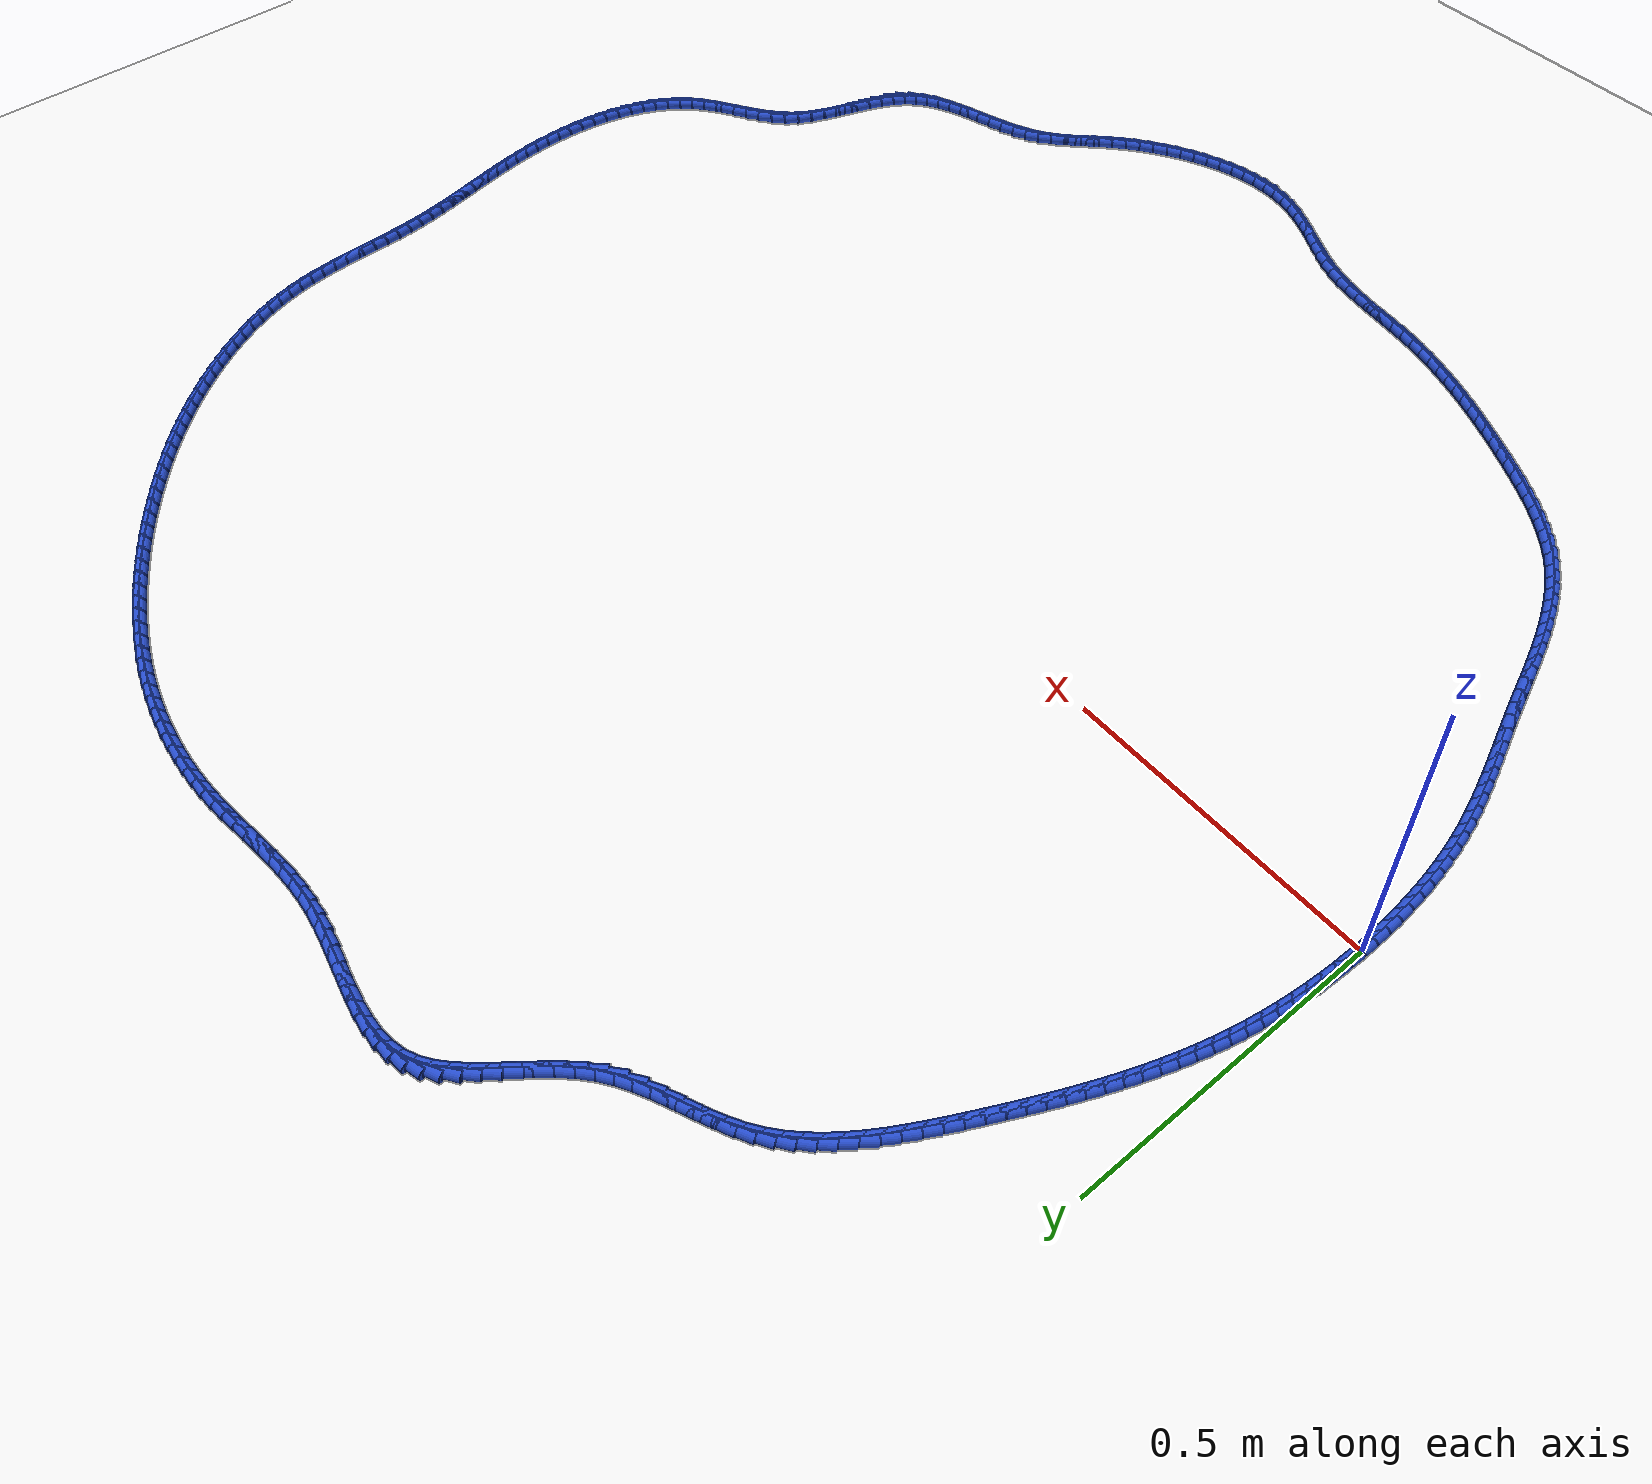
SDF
<sdf version="1.6">
 <world name="default">
  <light name="sun" type="directional">
   <pose>0 0 10 0 -0 0</pose>
   <diffuse>0.8 0.8 0.8 1</diffuse>
   <specular>0.2 0.2 0.2 1</specular>
   <attenuation>
    <range>1000</range>
    <constant>0.9</constant>
    <linear>0.01</linear>
    <quadratic>0.001</quadratic>
   </attenuation>
   <direction>-0.5 0.1 -0.9</direction>
  </light>
  <model name="ground_plane">
   <static>1</static>
   <link name="link">
    <collision name="collision">
     <geometry><plane><normal>0 0 1</normal><size>100 100</size></plane></geometry>
     <surface><friction><ode><mu>100</mu><mu2>50</mu2></ode></friction></surface>
    </collision>
    <visual name="visual">
     <cast_shadows>0</cast_shadows>
     <geometry><plane><normal>0 0 1</normal><size>100 100</size></plane></geometry>
     <material>
      <script><uri>file://media/materials/scripts/gazebo.material</uri><name>Gazebo/WhiteGlow</name></script>
     </material>
    </visual>
   </link>
  </model>
  <gravity>0 0 -9.8</gravity>
  <magnetic_field>6e-06 2.3e-05 -4.2e-05</magnetic_field>
  <atmosphere type="adiabatic"/>
  <physics name="default_physics" default="0" type="ode">
   <max_step_size>0.001</max_step_size>
   <real_time_factor>1</real_time_factor>
   <real_time_update_rate>1000</real_time_update_rate>
  </physics>
  <scene><ambient>0.4 0.4 0.4 1</ambient><background>0.7 0.7 0.7 1</background><shadows>1</shadows></scene>
  <spherical_coordinates>
   <surface_model>EARTH_WGS84</surface_model>
   <latitude_deg>0</latitude_deg>
   <longitude_deg>0</longitude_deg>
   <elevation>0</elevation>
   <heading_deg>0</heading_deg>
  </spherical_coordinates>
  <model name="line">
   <link name="link_0">
    <pose>1.1709383462843448e-17 8.326672684688674e-17 0.01 0 1.57 1.5553047397902697</pose>
    <collision name="collision">
     <geometry><cylinder><radius>0.01</radius><length>0.08</length></cylinder></geometry>
    </collision>
    <visual name="visual">
     <material>
      <script><name>Gazebo/Blue</name><uri>file://media/materials/scripts/gazebo.material</uri></script>
     </material>
     <geometry><cylinder><radius>0.01</radius><length>0.08</length></cylinder></geometry>
    </visual>
   </link>
   <link name="link_1">
    <pose>0.0003812467061995517 0.024607950575049647 0.01 0 1.57 1.532972883875322</pose>
    <collision name="collision">
     <geometry><cylinder><radius>0.01</radius><length>0.08</length></cylinder></geometry>
    </collision>
    <visual name="visual">
     <material>
      <script><name>Gazebo/Blue</name><uri>file://media/materials/scripts/gazebo.material</uri></script>
     </material>
     <geometry><cylinder><radius>0.01</radius><length>0.08</length></cylinder></geometry>
    </visual>
   </link>
   <link name="link_2">
    <pose>0.0013112480991377127 0.04918418658742195 0.01 0 1.57 1.5101342639521196</pose>
    <collision name="collision">
     <geometry><cylinder><radius>0.01</radius><length>0.08</length></cylinder></geometry>
    </collision>
    <visual name="visual">
     <material>
      <script><name>Gazebo/Blue</name><uri>file://media/materials/scripts/gazebo.material</uri></script>
     </material>
     <geometry><cylinder><radius>0.01</radius><length>0.08</length></cylinder></geometry>
    </visual>
   </link>
   <link name="link_3">
    <pose>0.0028006009073328216 0.07370569817742555 0.01 0 1.57 1.4867483651164621</pose>
    <collision name="collision">
     <geometry><cylinder><radius>0.01</radius><length>0.08</length></cylinder></geometry>
    </collision>
    <visual name="visual">
     <material>
      <script><name>Gazebo/Blue</name><uri>file://media/materials/scripts/gazebo.material</uri></script>
     </material>
     <geometry><cylinder><radius>0.01</radius><length>0.08</length></cylinder></geometry>
    </visual>
   </link>
   <link name="link_4">
    <pose>0.004859901859303199 0.09814947548536873 0.01 0 1.57 1.4627748649739634</pose>
    <collision name="collision">
     <geometry><cylinder><radius>0.01</radius><length>0.08</length></cylinder></geometry>
    </collision>
    <visual name="visual">
     <material>
      <script><name>Gazebo/Blue</name><uri>file://media/materials/scripts/gazebo.material</uri></script>
     </material>
     <geometry><cylinder><radius>0.01</radius><length>0.08</length></cylinder></geometry>
    </visual>
   </link>
   <link name="link_5">
    <pose>0.007499747683567175 0.12249250865156011 0.01 0 1.57 1.4381737925669953</pose>
    <collision name="collision">
     <geometry><cylinder><radius>0.01</radius><length>0.08</length></cylinder></geometry>
    </collision>
    <visual name="visual">
     <material>
      <script><name>Gazebo/Blue</name><uri>file://media/materials/scripts/gazebo.material</uri></script>
     </material>
     <geometry><cylinder><radius>0.01</radius><length>0.08</length></cylinder></geometry>
    </visual>
   </link>
   <link name="link_6">
    <pose>0.010730735108643075 0.14671178781630811 0.01 0 1.57 1.412905744207191</pose>
    <collision name="collision">
     <geometry><cylinder><radius>0.01</radius><length>0.08</length></cylinder></geometry>
    </collision>
    <visual name="visual">
     <material>
      <script><name>Gazebo/Blue</name><uri>file://media/materials/scripts/gazebo.material</uri></script>
     </material>
     <geometry><cylinder><radius>0.01</radius><length>0.08</length></cylinder></geometry>
    </visual>
   </link>
   <link name="link_7">
    <pose>0.014563460863049223 0.17078430311992115 0.01 0 1.57 1.386932162574718</pose>
    <collision name="collision">
     <geometry><cylinder><radius>0.01</radius><length>0.08</length></cylinder></geometry>
    </collision>
    <visual name="visual">
     <material>
      <script><name>Gazebo/Blue</name><uri>file://media/materials/scripts/gazebo.material</uri></script>
     </material>
     <geometry><cylinder><radius>0.01</radius><length>0.08</length></cylinder></geometry>
    </visual>
   </link>
   <link name="link_8">
    <pose>0.019008521675303938 0.19468704470270767 0.01 0 1.57 1.3602156854906027</pose>
    <collision name="collision">
     <geometry><cylinder><radius>0.01</radius><length>0.08</length></cylinder></geometry>
    </collision>
    <visual name="visual">
     <material>
      <script><name>Gazebo/Blue</name><uri>file://media/materials/scripts/gazebo.material</uri></script>
     </material>
     <geometry><cylinder><radius>0.01</radius><length>0.08</length></cylinder></geometry>
    </visual>
   </link>
   <link name="link_9">
    <pose>0.02407651427392555 0.21839700270497614 0.01 0 1.57 1.3327609385936665</pose>
    <collision name="collision">
     <geometry><cylinder><radius>0.01</radius><length>0.08</length></cylinder></geometry>
    </collision>
    <visual name="visual">
     <material>
      <script><name>Gazebo/Blue</name><uri>file://media/materials/scripts/gazebo.material</uri></script>
     </material>
     <geometry><cylinder><radius>0.01</radius><length>0.08</length></cylinder></geometry>
    </visual>
   </link>
   <link name="link_10">
    <pose>0.02977723821603783 0.24189202076844585 0.01 0 1.57 1.3055738209807342</pose>
    <collision name="collision">
     <geometry><cylinder><radius>0.01</radius><length>0.08</length></cylinder></geometry>
    </collision>
    <visual name="visual">
     <material>
      <script><name>Gazebo/Blue</name><uri>file://media/materials/scripts/gazebo.material</uri></script>
     </material>
     <geometry><cylinder><radius>0.01</radius><length>0.08</length></cylinder></geometry>
    </visual>
   </link>
   <link name="link_11">
    <pose>0.03610042501301905 0.2651714286361586 0.01 0 1.57 1.2797929943238218</pose>
    <collision name="collision">
     <geometry><cylinder><radius>0.01</radius><length>0.08</length></cylinder></geometry>
    </collision>
    <visual name="visual">
     <material>
      <script><name>Gazebo/Blue</name><uri>file://media/materials/scripts/gazebo.material</uri></script>
     </material>
     <geometry><cylinder><radius>0.01</radius><length>0.08</length></cylinder></geometry>
    </visual>
   </link>
   <link name="link_12">
    <pose>0.04301472529116708 0.2882571265614364 0.01 0 1.57 1.255550255592976</pose>
    <collision name="collision">
     <geometry><cylinder><radius>0.01</radius><length>0.08</length></cylinder></geometry>
    </collision>
    <visual name="visual">
     <material>
      <script><name>Gazebo/Blue</name><uri>file://media/materials/scripts/gazebo.material</uri></script>
     </material>
     <geometry><cylinder><radius>0.01</radius><length>0.08</length></cylinder></geometry>
    </visual>
   </link>
   <link name="link_13">
    <pose>0.050487789783555295 0.3111720853456462 0.01 0 1.57 1.2329104635235668</pose>
    <collision name="collision">
     <geometry><cylinder><radius>0.01</radius><length>0.08</length></cylinder></geometry>
    </collision>
    <visual name="visual">
     <material>
      <script><name>Gazebo/Blue</name><uri>file://media/materials/scripts/gazebo.material</uri></script>
     </material>
     <geometry><cylinder><radius>0.01</radius><length>0.08</length></cylinder></geometry>
    </visual>
   </link>
   <link name="link_14">
    <pose>0.05848726922325713 0.333939275790155 0.01 0 1.57 1.2119231385453824</pose>
    <collision name="collision">
     <geometry><cylinder><radius>0.01</radius><length>0.08</length></cylinder></geometry>
    </collision>
    <visual name="visual">
     <material>
      <script><name>Gazebo/Blue</name><uri>file://media/materials/scripts/gazebo.material</uri></script>
     </material>
     <geometry><cylinder><radius>0.01</radius><length>0.08</length></cylinder></geometry>
    </visual>
   </link>
   <link name="link_15">
    <pose>0.06698081434334588 0.3565816686963294 0.01 0 1.57 1.192623739514269</pose>
    <collision name="collision">
     <geometry><cylinder><radius>0.01</radius><length>0.08</length></cylinder></geometry>
    </collision>
    <visual name="visual">
     <material>
      <script><name>Gazebo/Blue</name><uri>file://media/materials/scripts/gazebo.material</uri></script>
     </material>
     <geometry><cylinder><radius>0.01</radius><length>0.08</length></cylinder></geometry>
    </visual>
   </link>
   <link name="link_16">
    <pose>0.07593607587689495 0.37912223486553637 0.01 0 1.57 1.1750351339731673</pose>
    <collision name="collision">
     <geometry><cylinder><radius>0.01</radius><length>0.08</length></cylinder></geometry>
    </collision>
    <visual name="visual">
     <material>
      <script><name>Gazebo/Blue</name><uri>file://media/materials/scripts/gazebo.material</uri></script>
     </material>
     <geometry><cylinder><radius>0.01</radius><length>0.08</length></cylinder></geometry>
    </visual>
   </link>
   <link name="link_17">
    <pose>0.08532070455697777 0.40158394509914286 0.01 0 1.57 1.1591691599053073</pose>
    <collision name="collision">
     <geometry><cylinder><radius>0.01</radius><length>0.08</length></cylinder></geometry>
    </collision>
    <visual name="visual">
     <material>
      <script><name>Gazebo/Blue</name><uri>file://media/materials/scripts/gazebo.material</uri></script>
     </material>
     <geometry><cylinder><radius>0.01</radius><length>0.08</length></cylinder></geometry>
    </visual>
   </link>
   <link name="link_18">
    <pose>0.09510235111666764 0.4239897701985157 0.01 0 1.57 1.1450281935200248</pose>
    <collision name="collision">
     <geometry><cylinder><radius>0.01</radius><length>0.08</length></cylinder></geometry>
    </collision>
    <visual name="visual">
     <material>
      <script><name>Gazebo/Blue</name><uri>file://media/materials/scripts/gazebo.material</uri></script>
     </material>
     <geometry><cylinder><radius>0.01</radius><length>0.08</length></cylinder></geometry>
    </visual>
   </link>
   <link name="link_19">
    <pose>0.10524866628903799 0.44636268096502163 0.01 0 1.57 1.132606655979784</pose>
    <collision name="collision">
     <geometry><cylinder><radius>0.01</radius><length>0.08</length></cylinder></geometry>
    </collision>
    <visual name="visual">
     <material>
      <script><name>Gazebo/Blue</name><uri>file://media/materials/scripts/gazebo.material</uri></script>
     </material>
     <geometry><cylinder><radius>0.01</radius><length>0.08</length></cylinder></geometry>
    </visual>
   </link>
   <link name="link_20">
    <pose>0.11572730080716219 0.4687256482000277 0.01 0 1.57 1.1218924100314067</pose>
    <collision name="collision">
     <geometry><cylinder><radius>0.01</radius><length>0.08</length></cylinder></geometry>
    </collision>
    <visual name="visual">
     <material>
      <script><name>Gazebo/Blue</name><uri>file://media/materials/scripts/gazebo.material</uri></script>
     </material>
     <geometry><cylinder><radius>0.01</radius><length>0.08</length></cylinder></geometry>
    </visual>
   </link>
   <link name="link_21">
    <pose>0.1265059054041136 0.49110164270490064 0.01 0 1.57 1.112868013838958</pose>
    <collision name="collision">
     <geometry><cylinder><radius>0.01</radius><length>0.08</length></cylinder></geometry>
    </collision>
    <visual name="visual">
     <material>
      <script><name>Gazebo/Blue</name><uri>file://media/materials/scripts/gazebo.material</uri></script>
     </material>
     <geometry><cylinder><radius>0.01</radius><length>0.08</length></cylinder></geometry>
    </visual>
   </link>
   <link name="link_22">
    <pose>0.13755213081296566 0.5135136352810075 0.01 0 1.57 1.10551181315561</pose>
    <collision name="collision">
     <geometry><cylinder><radius>0.01</radius><length>0.08</length></cylinder></geometry>
    </collision>
    <visual name="visual">
     <material>
      <script><name>Gazebo/Blue</name><uri>file://media/materials/scripts/gazebo.material</uri></script>
     </material>
     <geometry><cylinder><radius>0.01</radius><length>0.08</length></cylinder></geometry>
    </visual>
   </link>
   <link name="link_23">
    <pose>0.14883362776679163 0.5359845967297147 0.01 0 1.57 1.0986149254631403</pose>
    <collision name="collision">
     <geometry><cylinder><radius>0.01</radius><length>0.08</length></cylinder></geometry>
    </collision>
    <visual name="visual">
     <material>
      <script><name>Gazebo/Blue</name><uri>file://media/materials/scripts/gazebo.material</uri></script>
     </material>
     <geometry><cylinder><radius>0.01</radius><length>0.08</length></cylinder></geometry>
    </visual>
   </link>
   <link name="link_24">
    <pose>0.16033753742915416 0.5585097818580833 0.01 0 1.57 1.0865495148317468</pose>
    <collision name="collision">
     <geometry><cylinder><radius>0.01</radius><length>0.08</length></cylinder></geometry>
    </collision>
    <visual name="visual">
     <material>
      <script><name>Gazebo/Blue</name><uri>file://media/materials/scripts/gazebo.material</uri></script>
     </material>
     <geometry><cylinder><radius>0.01</radius><length>0.08</length></cylinder></geometry>
    </visual>
   </link>
   <link name="link_25">
    <pose>0.17214326349090753 0.5809532453089418 0.01 0 1.57 1.0675600212944543</pose>
    <collision name="collision">
     <geometry><cylinder><radius>0.01</radius><length>0.08</length></cylinder></geometry>
    </collision>
    <visual name="visual">
     <material>
      <script><name>Gazebo/Blue</name><uri>file://media/materials/scripts/gazebo.material</uri></script>
     </material>
     <geometry><cylinder><radius>0.01</radius><length>0.08</length></cylinder></geometry>
    </visual>
   </link>
   <link name="link_26">
    <pose>0.18435748294254106 0.6031402582504383 0.01 0 1.57 1.0414027347263328</pose>
    <collision name="collision">
     <geometry><cylinder><radius>0.01</radius><length>0.08</length></cylinder></geometry>
    </collision>
    <visual name="visual">
     <material>
      <script><name>Gazebo/Blue</name><uri>file://media/materials/scripts/gazebo.material</uri></script>
     </material>
     <geometry><cylinder><radius>0.01</radius><length>0.08</length></cylinder></geometry>
    </visual>
   </link>
   <link name="link_27">
    <pose>0.19708687685222578 0.6248960860521315 0.01 0 1.57 1.0077027396976996</pose>
    <collision name="collision">
     <geometry><cylinder><radius>0.01</radius><length>0.08</length></cylinder></geometry>
    </collision>
    <visual name="visual">
     <material>
      <script><name>Gazebo/Blue</name><uri>file://media/materials/scripts/gazebo.material</uri></script>
     </material>
     <geometry><cylinder><radius>0.01</radius><length>0.08</length></cylinder></geometry>
    </visual>
   </link>
   <link name="link_28">
    <pose>0.2104381262881325 0.6460459940835802 0.01 0 1.57 0.965982316597031</pose>
    <collision name="collision">
     <geometry><cylinder><radius>0.01</radius><length>0.08</length></cylinder></geometry>
    </collision>
    <visual name="visual">
     <material>
      <script><name>Gazebo/Blue</name><uri>file://media/materials/scripts/gazebo.material</uri></script>
     </material>
     <geometry><cylinder><radius>0.01</radius><length>0.08</length></cylinder></geometry>
    </visual>
   </link>
   <link name="link_29">
    <pose>0.22451791231843213 0.6664152477143426 0.01 0 1.57 0.9157073745038969</pose>
    <collision name="collision">
     <geometry><cylinder><radius>0.01</radius><length>0.08</length></cylinder></geometry>
    </collision>
    <visual name="visual">
     <material>
      <script><name>Gazebo/Blue</name><uri>file://media/materials/scripts/gazebo.material</uri></script>
     </material>
     <geometry><cylinder><radius>0.01</radius><length>0.08</length></cylinder></geometry>
    </visual>
   </link>
   <link name="link_30">
    <pose>0.2394329160112957 0.6858291123139778 0.01 0 1.57 0.8563623609497848</pose>
    <collision name="collision">
     <geometry><cylinder><radius>0.01</radius><length>0.08</length></cylinder></geometry>
    </collision>
    <visual name="visual">
     <material>
      <script><name>Gazebo/Blue</name><uri>file://media/materials/scripts/gazebo.material</uri></script>
     </material>
     <geometry><cylinder><radius>0.01</radius><length>0.08</length></cylinder></geometry>
    </visual>
   </link>
   <link name="link_31">
    <pose>0.2552898184348942 0.7041128532520444 0.01 0 1.57 0.7875643633255981</pose>
    <collision name="collision">
     <geometry><cylinder><radius>0.01</radius><length>0.08</length></cylinder></geometry>
    </collision>
    <visual name="visual">
     <material>
      <script><name>Gazebo/Blue</name><uri>file://media/materials/scripts/gazebo.material</uri></script>
     </material>
     <geometry><cylinder><radius>0.01</radius><length>0.08</length></cylinder></geometry>
    </visual>
   </link>
   <link name="link_32">
    <pose>0.2721953006573985 0.721091735898101 0.01 0 1.57 0.7092213361737795</pose>
    <collision name="collision">
     <geometry><cylinder><radius>0.01</radius><length>0.08</length></cylinder></geometry>
    </collision>
    <visual name="visual">
     <material>
      <script><name>Gazebo/Blue</name><uri>file://media/materials/scripts/gazebo.material</uri></script>
     </material>
     <geometry><cylinder><radius>0.01</radius><length>0.08</length></cylinder></geometry>
    </visual>
   </link>
   <link name="link_33">
    <pose>0.29025604374697955 0.7365910256217063 0.01 0 1.57 0.621749364934075</pose>
    <collision name="collision">
     <geometry><cylinder><radius>0.01</radius><length>0.08</length></cylinder></geometry>
    </collision>
    <visual name="visual">
     <material>
      <script><name>Gazebo/Blue</name><uri>file://media/materials/scripts/gazebo.material</uri></script>
     </material>
     <geometry><cylinder><radius>0.01</radius><length>0.08</length></cylinder></geometry>
    </visual>
   </link>
   <link name="link_34">
    <pose>0.30957838471305854 0.7504365121984696 0.01 0 1.57 0.5351738381544248</pose>
    <collision name="collision">
     <geometry><cylinder><radius>0.01</radius><length>0.08</length></cylinder></geometry>
    </collision>
    <visual name="visual">
     <material>
      <script><name>Gazebo/Blue</name><uri>file://media/materials/scripts/gazebo.material</uri></script>
     </material>
     <geometry><cylinder><radius>0.01</radius><length>0.08</length></cylinder></geometry>
    </visual>
   </link>
   <link name="link_35">
    <pose>0.3301507862072485 0.7626336466581581 0.01 0 1.57 0.47233671066272587</pose>
    <collision name="collision">
     <geometry><cylinder><radius>0.01</radius><length>0.08</length></cylinder></geometry>
    </collision>
    <visual name="visual">
     <material>
      <script><name>Gazebo/Blue</name><uri>file://media/materials/scripts/gazebo.material</uri></script>
     </material>
     <geometry><cylinder><radius>0.01</radius><length>0.08</length></cylinder></geometry>
    </visual>
   </link>
   <link name="link_36">
    <pose>0.3516722068185414 0.7736291351426894 0.01 0 1.57 0.43594813481928885</pose>
    <collision name="collision">
     <geometry><cylinder><radius>0.01</radius><length>0.08</length></cylinder></geometry>
    </collision>
    <visual name="visual">
     <material>
      <script><name>Gazebo/Blue</name><uri>file://media/materials/scripts/gazebo.material</uri></script>
     </material>
     <geometry><cylinder><radius>0.01</radius><length>0.08</length></cylinder></geometry>
    </visual>
   </link>
   <link name="link_37">
    <pose>0.3737979650538051 0.7839361989549681 0.01 0 1.57 0.4250222106125202</pose>
    <collision name="collision">
     <geometry><cylinder><radius>0.01</radius><length>0.08</length></cylinder></geometry>
    </collision>
    <visual name="visual">
     <material>
      <script><name>Gazebo/Blue</name><uri>file://media/materials/scripts/gazebo.material</uri></script>
     </material>
     <geometry><cylinder><radius>0.01</radius><length>0.08</length></cylinder></geometry>
    </visual>
   </link>
   <link name="link_38">
    <pose>0.39618337941990767 0.794068059397899 0.01 0 1.57 0.438945606494985</pose>
    <collision name="collision">
     <geometry><cylinder><radius>0.01</radius><length>0.08</length></cylinder></geometry>
    </collision>
    <visual name="visual">
     <material>
      <script><name>Gazebo/Blue</name><uri>file://media/materials/scripts/gazebo.material</uri></script>
     </material>
     <geometry><cylinder><radius>0.01</radius><length>0.08</length></cylinder></geometry>
    </visual>
   </link>
   <link name="link_39">
    <pose>0.41848376842371715 0.8045379377743868 0.01 0 1.57 0.47765901131718896</pose>
    <collision name="collision">
     <geometry><cylinder><radius>0.01</radius><length>0.08</length></cylinder></geometry>
    </collision>
    <visual name="visual">
     <material>
      <script><name>Gazebo/Blue</name><uri>file://media/materials/scripts/gazebo.material</uri></script>
     </material>
     <geometry><cylinder><radius>0.01</radius><length>0.08</length></cylinder></geometry>
    </visual>
   </link>
   <link name="link_40">
    <pose>0.4403544505721013 0.8158590553873359 0.01 0 1.57 0.5413879484975384</pose>
    <collision name="collision">
     <geometry><cylinder><radius>0.01</radius><length>0.08</length></cylinder></geometry>
    </collision>
    <visual name="visual">
     <material>
      <script><name>Gazebo/Blue</name><uri>file://media/materials/scripts/gazebo.material</uri></script>
     </material>
     <geometry><cylinder><radius>0.01</radius><length>0.08</length></cylinder></geometry>
    </visual>
   </link>
   <link name="link_41">
    <pose>0.4614507443719284 0.8285446335396514 0.01 0 1.57 0.629920634023518</pose>
    <collision name="collision">
     <geometry><cylinder><radius>0.01</radius><length>0.08</length></cylinder></geometry>
    </collision>
    <visual name="visual">
     <material>
      <script><name>Gazebo/Blue</name><uri>file://media/materials/scripts/gazebo.material</uri></script>
     </material>
     <geometry><cylinder><radius>0.01</radius><length>0.08</length></cylinder></geometry>
    </visual>
   </link>
   <link name="link_42">
    <pose>0.4814279683300667 0.8431078935342381 0.01 0 1.57 0.7352961015194527</pose>
    <collision name="collision">
     <geometry><cylinder><radius>0.01</radius><length>0.08</length></cylinder></geometry>
    </collision>
    <visual name="visual">
     <material>
      <script><name>Gazebo/Blue</name><uri>file://media/materials/scripts/gazebo.material</uri></script>
     </material>
     <geometry><cylinder><radius>0.01</radius><length>0.08</length></cylinder></geometry>
    </visual>
   </link>
   <link name="link_43">
    <pose>0.5000197860493675 0.8599242050861123 0.01 0 1.57 0.8209705645857384</pose>
    <collision name="collision">
     <geometry><cylinder><radius>0.01</radius><length>0.08</length></cylinder></geometry>
    </collision>
    <visual name="visual">
     <material>
      <script><name>Gazebo/Blue</name><uri>file://media/materials/scripts/gazebo.material</uri></script>
     </material>
     <geometry><cylinder><radius>0.01</radius><length>0.08</length></cylinder></geometry>
    </visual>
   </link>
   <link name="link_44">
    <pose>0.5174026098041652 0.8785899024565383 0.01 0 1.57 0.876834590053963</pose>
    <collision name="collision">
     <geometry><cylinder><radius>0.01</radius><length>0.08</length></cylinder></geometry>
    </collision>
    <visual name="visual">
     <material>
      <script><name>Gazebo/Blue</name><uri>file://media/materials/scripts/gazebo.material</uri></script>
     </material>
     <geometry><cylinder><radius>0.01</radius><length>0.08</length></cylinder></geometry>
    </visual>
   </link>
   <link name="link_45">
    <pose>0.5339082216809343 0.8984279399964671 0.01 0 1.57 0.9053018156907789</pose>
    <collision name="collision">
     <geometry><cylinder><radius>0.01</radius><length>0.08</length></cylinder></geometry>
    </collision>
    <visual name="visual">
     <material>
      <script><name>Gazebo/Blue</name><uri>file://media/materials/scripts/gazebo.material</uri></script>
     </material>
     <geometry><cylinder><radius>0.01</radius><length>0.08</length></cylinder></geometry>
    </visual>
   </link>
   <link name="link_46">
    <pose>0.5498685723140785 0.9187609754894721 0.01 0 1.57 0.9074604498584998</pose>
    <collision name="collision">
     <geometry><cylinder><radius>0.01</radius><length>0.08</length></cylinder></geometry>
    </collision>
    <visual name="visual">
     <material>
      <script><name>Gazebo/Blue</name><uri>file://media/materials/scripts/gazebo.material</uri></script>
     </material>
     <geometry><cylinder><radius>0.01</radius><length>0.08</length></cylinder></geometry>
    </visual>
   </link>
   <link name="link_47">
    <pose>0.5656156123380017 0.9389116667191277 0.01 0 1.57 0.8825218700833308</pose>
    <collision name="collision">
     <geometry><cylinder><radius>0.01</radius><length>0.08</length></cylinder></geometry>
    </collision>
    <visual name="visual">
     <material>
      <script><name>Gazebo/Blue</name><uri>file://media/materials/scripts/gazebo.material</uri></script>
     </material>
     <geometry><cylinder><radius>0.01</radius><length>0.08</length></cylinder></geometry>
    </visual>
   </link>
   <link name="link_48">
    <pose>0.5814812923871078 0.9582026714690081 0.01 0 1.57 0.8275714090057353</pose>
    <collision name="collision">
     <geometry><cylinder><radius>0.01</radius><length>0.08</length></cylinder></geometry>
    </collision>
    <visual name="visual">
     <material>
      <script><name>Gazebo/Blue</name><uri>file://media/materials/scripts/gazebo.material</uri></script>
     </material>
     <geometry><cylinder><radius>0.01</radius><length>0.08</length></cylinder></geometry>
    </visual>
   </link>
   <link name="link_49">
    <pose>0.5977975630958002 0.9759566475226866 0.01 0 1.57 0.7376623204582835</pose>
    <collision name="collision">
     <geometry><cylinder><radius>0.01</radius><length>0.08</length></cylinder></geometry>
    </collision>
    <visual name="visual">
     <material>
      <script><name>Gazebo/Blue</name><uri>file://media/materials/scripts/gazebo.material</uri></script>
     </material>
     <geometry><cylinder><radius>0.01</radius><length>0.08</length></cylinder></geometry>
    </visual>
   </link>
   <link name="link_50">
    <pose>0.6148963750984827 0.9914962526637376 0.01 0 1.57 0.6069789326414792</pose>
    <collision name="collision">
     <geometry><cylinder><radius>0.01</radius><length>0.08</length></cylinder></geometry>
    </collision>
    <visual name="visual">
     <material>
      <script><name>Gazebo/Blue</name><uri>file://media/materials/scripts/gazebo.material</uri></script>
     </material>
     <geometry><cylinder><radius>0.01</radius><length>0.08</length></cylinder></geometry>
    </visual>
   </link>
   <link name="link_51">
    <pose>0.6331096790295591 1.0041441446757349 0.01 0 1.57 0.434400613854901</pose>
    <collision name="collision">
     <geometry><cylinder><radius>0.01</radius><length>0.08</length></cylinder></geometry>
    </collision>
    <visual name="visual">
     <material>
      <script><name>Gazebo/Blue</name><uri>file://media/materials/scripts/gazebo.material</uri></script>
     </material>
     <geometry><cylinder><radius>0.01</radius><length>0.08</length></cylinder></geometry>
    </visual>
   </link>
   <link name="link_52">
    <pose>0.6527539873177739 1.013258279415138 0.01 0 1.57 0.25733779516104544</pose>
    <collision name="collision">
     <geometry><cylinder><radius>0.01</radius><length>0.08</length></cylinder></geometry>
    </collision>
    <visual name="visual">
     <material>
      <script><name>Gazebo/Blue</name><uri>file://media/materials/scripts/gazebo.material</uri></script>
     </material>
     <geometry><cylinder><radius>0.01</radius><length>0.08</length></cylinder></geometry>
    </visual>
   </link>
   <link name="link_53">
    <pose>0.6738746243924979 1.018816659781345 0.01 0 1.57 0.11152506230391843</pose>
    <collision name="collision">
     <geometry><cylinder><radius>0.01</radius><length>0.08</length></cylinder></geometry>
    </collision>
    <visual name="visual">
     <material>
      <script><name>Gazebo/Blue</name><uri>file://media/materials/scripts/gazebo.material</uri></script>
     </material>
     <geometry><cylinder><radius>0.01</radius><length>0.08</length></cylinder></geometry>
    </visual>
   </link>
   <link name="link_54">
    <pose>0.6962854789147273 1.0213264458051317 0.01 0 1.57 -0.0006241185811978061</pose>
    <collision name="collision">
     <geometry><cylinder><radius>0.01</radius><length>0.08</length></cylinder></geometry>
    </collision>
    <visual name="visual">
     <material>
      <script><name>Gazebo/Blue</name><uri>file://media/materials/scripts/gazebo.material</uri></script>
     </material>
     <geometry><cylinder><radius>0.01</radius><length>0.08</length></cylinder></geometry>
    </visual>
   </link>
   <link name="link_55">
    <pose>0.7197930144581903 1.0213117743134958 0.01 0 1.57 -0.08235879660350288</pose>
    <collision name="collision">
     <geometry><cylinder><radius>0.01</radius><length>0.08</length></cylinder></geometry>
    </collision>
    <visual name="visual">
     <material>
      <script><name>Gazebo/Blue</name><uri>file://media/materials/scripts/gazebo.material</uri></script>
     </material>
     <geometry><cylinder><radius>0.01</radius><length>0.08</length></cylinder></geometry>
    </visual>
   </link>
   <link name="link_56">
    <pose>0.7442036945966158 1.0192967821334362 0.01 0 1.57 -0.13809378365272365</pose>
    <collision name="collision">
     <geometry><cylinder><radius>0.01</radius><length>0.08</length></cylinder></geometry>
    </collision>
    <visual name="visual">
     <material>
      <script><name>Gazebo/Blue</name><uri>file://media/materials/scripts/gazebo.material</uri></script>
     </material>
     <geometry><cylinder><radius>0.01</radius><length>0.08</length></cylinder></geometry>
    </visual>
   </link>
   <link name="link_57">
    <pose>0.7693239829037316 1.0158056060919507 0.01 0 1.57 -0.17161244095150074</pose>
    <collision name="collision">
     <geometry><cylinder><radius>0.01</radius><length>0.08</length></cylinder></geometry>
    </collision>
    <visual name="visual">
     <material>
      <script><name>Gazebo/Blue</name><uri>file://media/materials/scripts/gazebo.material</uri></script>
     </material>
     <geometry><cylinder><radius>0.01</radius><length>0.08</length></cylinder></geometry>
    </visual>
   </link>
   <link name="link_58">
    <pose>0.794960342953267 1.0113623830160376 0.01 0 1.57 -0.18549086339894721</pose>
    <collision name="collision">
     <geometry><cylinder><radius>0.01</radius><length>0.08</length></cylinder></geometry>
    </collision>
    <visual name="visual">
     <material>
      <script><name>Gazebo/Blue</name><uri>file://media/materials/scripts/gazebo.material</uri></script>
     </material>
     <geometry><cylinder><radius>0.01</radius><length>0.08</length></cylinder></geometry>
    </visual>
   </link>
   <link name="link_59">
    <pose>0.8209192383189501 1.0064912497326954 0.01 0 1.57 -0.18102774963708193</pose>
    <collision name="collision">
     <geometry><cylinder><radius>0.01</radius><length>0.08</length></cylinder></geometry>
    </collision>
    <visual name="visual">
     <material>
      <script><name>Gazebo/Blue</name><uri>file://media/materials/scripts/gazebo.material</uri></script>
     </material>
     <geometry><cylinder><radius>0.01</radius><length>0.08</length></cylinder></geometry>
    </visual>
   </link>
   <link name="link_60">
    <pose>0.84700713257451 1.0017163430689227 0.01 0 1.57 -0.15831076920506565</pose>
    <collision name="collision">
     <geometry><cylinder><radius>0.01</radius><length>0.08</length></cylinder></geometry>
    </collision>
    <visual name="visual">
     <material>
      <script><name>Gazebo/Blue</name><uri>file://media/materials/scripts/gazebo.material</uri></script>
     </material>
     <geometry><cylinder><radius>0.01</radius><length>0.08</length></cylinder></geometry>
    </visual>
   </link>
   <link name="link_61">
    <pose>0.8730304892936744 0.9975617998517172 0.01 0 1.57 -0.1162984420375153</pose>
    <collision name="collision">
     <geometry><cylinder><radius>0.01</radius><length>0.08</length></cylinder></geometry>
    </collision>
    <visual name="visual">
     <material>
      <script><name>Gazebo/Blue</name><uri>file://media/materials/scripts/gazebo.material</uri></script>
     </material>
     <geometry><cylinder><radius>0.01</radius><length>0.08</length></cylinder></geometry>
    </visual>
   </link>
   <link name="link_62">
    <pose>0.8987957727883813 0.9945517546545616 0.01 0 1.57 -0.058302131195823316</pose>
    <collision name="collision">
     <geometry><cylinder><radius>0.01</radius><length>0.08</length></cylinder></geometry>
    </collision>
    <visual name="visual">
     <material>
      <script><name>Gazebo/Blue</name><uri>file://media/materials/scripts/gazebo.material</uri></script>
     </material>
     <geometry><cylinder><radius>0.01</radius><length>0.08</length></cylinder></geometry>
    </visual>
   </link>
   <link name="link_63">
    <pose>0.9241549012278949 0.9930715859416128 0.01 0 1.57 -0.003137405123413332</pose>
    <collision name="collision">
     <geometry><cylinder><radius>0.01</radius><length>0.08</length></cylinder></geometry>
    </collision>
    <visual name="visual">
     <material>
      <script><name>Gazebo/Blue</name><uri>file://media/materials/scripts/gazebo.material</uri></script>
     </material>
     <geometry><cylinder><radius>0.01</radius><length>0.08</length></cylinder></geometry>
    </visual>
   </link>
   <link name="link_64">
    <pose>0.9491279850156418 0.992993235003512 0.01 0 1.57 0.04365785091011454</pose>
    <collision name="collision">
     <geometry><cylinder><radius>0.01</radius><length>0.08</length></cylinder></geometry>
    </collision>
    <visual name="visual">
     <material>
      <script><name>Gazebo/Blue</name><uri>file://media/materials/scripts/gazebo.material</uri></script>
     </material>
     <geometry><cylinder><radius>0.01</radius><length>0.08</length></cylinder></geometry>
    </visual>
   </link>
   <link name="link_65">
    <pose>0.9737740284691966 0.9940699124329798 0.01 0 1.57 0.08124320058380775</pose>
    <collision name="collision">
     <geometry><cylinder><radius>0.01</radius><length>0.08</length></cylinder></geometry>
    </collision>
    <visual name="visual">
     <material>
      <script><name>Gazebo/Blue</name><uri>file://media/materials/scripts/gazebo.material</uri></script>
     </material>
     <geometry><cylinder><radius>0.01</radius><length>0.08</length></cylinder></geometry>
    </visual>
   </link>
   <link name="link_66">
    <pose>0.9981520359061348 0.9960548288227374 0.01 0 1.57 0.1090598804364658</pose>
    <collision name="collision">
     <geometry><cylinder><radius>0.01</radius><length>0.08</length></cylinder></geometry>
    </collision>
    <visual name="visual">
     <material>
      <script><name>Gazebo/Blue</name><uri>file://media/materials/scripts/gazebo.material</uri></script>
     </material>
     <geometry><cylinder><radius>0.01</radius><length>0.08</length></cylinder></geometry>
    </visual>
   </link>
   <link name="link_67">
    <pose>1.0223210116440298 0.9987011947655052 0.01 0 1.57 0.12675883229389698</pose>
    <collision name="collision">
     <geometry><cylinder><radius>0.01</radius><length>0.08</length></cylinder></geometry>
    </collision>
    <visual name="visual">
     <material>
      <script><name>Gazebo/Blue</name><uri>file://media/materials/scripts/gazebo.material</uri></script>
     </material>
     <geometry><cylinder><radius>0.01</radius><length>0.08</length></cylinder></geometry>
    </visual>
   </link>
   <link name="link_68">
    <pose>1.0463399600004577 1.0017622208540045 0.01 0 1.57 0.13413237032126427</pose>
    <collision name="collision">
     <geometry><cylinder><radius>0.01</radius><length>0.08</length></cylinder></geometry>
    </collision>
    <visual name="visual">
     <material>
      <script><name>Gazebo/Blue</name><uri>file://media/materials/scripts/gazebo.material</uri></script>
     </material>
     <geometry><cylinder><radius>0.01</radius><length>0.08</length></cylinder></geometry>
    </visual>
   </link>
   <link name="link_69">
    <pose>1.0702678852929923 1.0049911176809554 0.01 0 1.57 0.13106515166974297</pose>
    <collision name="collision">
     <geometry><cylinder><radius>0.01</radius><length>0.08</length></cylinder></geometry>
    </collision>
    <visual name="visual">
     <material>
      <script><name>Gazebo/Blue</name><uri>file://media/materials/scripts/gazebo.material</uri></script>
     </material>
     <geometry><cylinder><radius>0.01</radius><length>0.08</length></cylinder></geometry>
    </visual>
   </link>
   <link name="link_70">
    <pose>1.0941637918392082 1.0081410958390793 0.01 0 1.57 0.11751328469925262</pose>
    <collision name="collision">
     <geometry><cylinder><radius>0.01</radius><length>0.08</length></cylinder></geometry>
    </collision>
    <visual name="visual">
     <material>
      <script><name>Gazebo/Blue</name><uri>file://media/materials/scripts/gazebo.material</uri></script>
     </material>
     <geometry><cylinder><radius>0.01</radius><length>0.08</length></cylinder></geometry>
    </visual>
   </link>
   <link name="link_71">
    <pose>1.1180866839566808 1.010965365921096 0.01 0 1.57 0.09351558838796674</pose>
    <collision name="collision">
     <geometry><cylinder><radius>0.01</radius><length>0.08</length></cylinder></geometry>
    </collision>
    <visual name="visual">
     <material>
      <script><name>Gazebo/Blue</name><uri>file://media/materials/scripts/gazebo.material</uri></script>
     </material>
     <geometry><cylinder><radius>0.01</radius><length>0.08</length></cylinder></geometry>
    </visual>
   </link>
   <link name="link_72">
    <pose>1.1420955659629843 1.0132171385197275 0.01 0 1.57 0.05943513696736095</pose>
    <collision name="collision">
     <geometry><cylinder><radius>0.01</radius><length>0.08</length></cylinder></geometry>
    </collision>
    <visual name="visual">
     <material>
      <script><name>Gazebo/Blue</name><uri>file://media/materials/scripts/gazebo.material</uri></script>
     </material>
     <geometry><cylinder><radius>0.01</radius><length>0.08</length></cylinder></geometry>
    </visual>
   </link>
   <link name="link_73">
    <pose>1.166247492413443 1.0146543042546685 0.01 0 1.57 0.02066032458123422</pose>
    <collision name="collision">
     <geometry><cylinder><radius>0.01</radius><length>0.08</length></cylinder></geometry>
    </collision>
    <visual name="visual">
     <material>
      <script><name>Gazebo/Blue</name><uri>file://media/materials/scripts/gazebo.material</uri></script>
     </material>
     <geometry><cylinder><radius>0.01</radius><length>0.08</length></cylinder></geometry>
    </visual>
   </link>
   <link name="link_74">
    <pose>1.19054881799123 1.0151564489775526 0.01 0 1.57 -0.017341846930867152</pose>
    <collision name="collision">
     <geometry><cylinder><radius>0.01</radius><length>0.08</length></cylinder></geometry>
    </collision>
    <visual name="visual">
     <material>
      <script><name>Gazebo/Blue</name><uri>file://media/materials/scripts/gazebo.material</uri></script>
     </material>
     <geometry><cylinder><radius>0.01</radius><length>0.08</length></cylinder></geometry>
    </visual>
   </link>
   <link name="link_75">
    <pose>1.2149517139981316 1.0147332152617599 0.01 0 1.57 -0.05444093672511951</pose>
    <collision name="collision">
     <geometry><cylinder><radius>0.01</radius><length>0.08</length></cylinder></geometry>
    </collision>
    <visual name="visual">
     <material>
      <script><name>Gazebo/Blue</name><uri>file://media/materials/scripts/gazebo.material</uri></script>
     </material>
     <geometry><cylinder><radius>0.01</radius><length>0.08</length></cylinder></geometry>
    </visual>
   </link>
   <link name="link_76">
    <pose>1.2394057043072917 1.0134006003208098 0.01 0 1.57 -0.0907755837551149</pose>
    <collision name="collision">
     <geometry><cylinder><radius>0.01</radius><length>0.08</length></cylinder></geometry>
    </collision>
    <visual name="visual">
     <material>
      <script><name>Gazebo/Blue</name><uri>file://media/materials/scripts/gazebo.material</uri></script>
     </material>
     <geometry><cylinder><radius>0.01</radius><length>0.08</length></cylinder></geometry>
    </visual>
   </link>
   <link name="link_77">
    <pose>1.2638603127918537 1.0111746013682232 0.01 0 1.57 -0.12648432738134088</pose>
    <collision name="collision">
     <geometry><cylinder><radius>0.01</radius><length>0.08</length></cylinder></geometry>
    </collision>
    <visual name="visual">
     <material>
      <script><name>Gazebo/Blue</name><uri>file://media/materials/scripts/gazebo.material</uri></script>
     </material>
     <geometry><cylinder><radius>0.01</radius><length>0.08</length></cylinder></geometry>
    </visual>
   </link>
   <link name="link_78">
    <pose>1.2882650633249617 1.0080712156175204 0.01 0 1.57 -0.16170547013847694</pose>
    <collision name="collision">
     <geometry><cylinder><radius>0.01</radius><length>0.08</length></cylinder></geometry>
    </collision>
    <visual name="visual">
     <material>
      <script><name>Gazebo/Blue</name><uri>file://media/materials/scripts/gazebo.material</uri></script>
     </material>
     <geometry><cylinder><radius>0.01</radius><length>0.08</length></cylinder></geometry>
    </visual>
   </link>
   <link name="link_79">
    <pose>1.3125694797797596 1.0041064402822222 0.01 0 1.57 -0.19657720367277795</pose>
    <collision name="collision">
     <geometry><cylinder><radius>0.01</radius><length>0.08</length></cylinder></geometry>
    </collision>
    <visual name="visual">
     <material>
      <script><name>Gazebo/Blue</name><uri>file://media/materials/scripts/gazebo.material</uri></script>
     </material>
     <geometry><cylinder><radius>0.01</radius><length>0.08</length></cylinder></geometry>
    </visual>
   </link>
   <link name="link_80">
    <pose>1.3367230860293904 0.9992962725758491 0.01 0 1.57 -0.23123793736708653</pose>
    <collision name="collision">
     <geometry><cylinder><radius>0.01</radius><length>0.08</length></cylinder></geometry>
    </collision>
    <visual name="visual">
     <material>
      <script><name>Gazebo/Blue</name><uri>file://media/materials/scripts/gazebo.material</uri></script>
     </material>
     <geometry><cylinder><radius>0.01</radius><length>0.08</length></cylinder></geometry>
    </visual>
   </link>
   <link name="link_81">
    <pose>1.3606754059469992 0.9936567097119211 0.01 0 1.57 -0.26582677831998064</pose>
    <collision name="collision">
     <geometry><cylinder><radius>0.01</radius><length>0.08</length></cylinder></geometry>
    </collision>
    <visual name="visual">
     <material>
      <script><name>Gazebo/Blue</name><uri>file://media/materials/scripts/gazebo.material</uri></script>
     </material>
     <geometry><cylinder><radius>0.01</radius><length>0.08</length></cylinder></geometry>
    </visual>
   </link>
   <link name="link_82">
    <pose>1.3843759634057289 0.9872037489039587 0.01 0 1.57 -0.3003779266260646</pose>
    <collision name="collision">
     <geometry><cylinder><radius>0.01</radius><length>0.08</length></cylinder></geometry>
    </collision>
    <visual name="visual">
     <material>
      <script><name>Gazebo/Blue</name><uri>file://media/materials/scripts/gazebo.material</uri></script>
     </material>
     <geometry><cylinder><radius>0.01</radius><length>0.08</length></cylinder></geometry>
    </visual>
   </link>
   <link name="link_83">
    <pose>1.4077774732487403 0.9799551221489016 0.01 0 1.57 -0.3337257662392503</pose>
    <collision name="collision">
     <geometry><cylinder><radius>0.01</radius><length>0.08</length></cylinder></geometry>
    </collision>
    <visual name="visual">
     <material>
      <script><name>Gazebo/Blue</name><uri>file://media/materials/scripts/gazebo.material</uri></script>
     </material>
     <geometry><cylinder><radius>0.01</radius><length>0.08</length></cylinder></geometry>
    </visual>
   </link>
   <link name="link_84">
    <pose>1.4308702649676968 0.9719490107955119 0.01 0 1.57 -0.3650044388943449</pose>
    <collision name="collision">
     <geometry><cylinder><radius>0.01</radius><length>0.08</length></cylinder></geometry>
    </collision>
    <visual name="visual">
     <material>
      <script><name>Gazebo/Blue</name><uri>file://media/materials/scripts/gazebo.material</uri></script>
     </material>
     <geometry><cylinder><radius>0.01</radius><length>0.08</length></cylinder></geometry>
    </visual>
   </link>
   <link name="link_85">
    <pose>1.453669184606701 0.9632369247128563 0.01 0 1.57 -0.39414239050209127</pose>
    <collision name="collision">
     <geometry><cylinder><radius>0.01</radius><length>0.08</length></cylinder></geometry>
    </collision>
    <visual name="visual">
     <material>
      <script><name>Gazebo/Blue</name><uri>file://media/materials/scripts/gazebo.material</uri></script>
     </material>
     <geometry><cylinder><radius>0.01</radius><length>0.08</length></cylinder></geometry>
    </visual>
   </link>
   <link name="link_86">
    <pose>1.4761894981548054 0.9538706020747276 0.01 0 1.57 -0.4211032966922181</pose>
    <collision name="collision">
     <geometry><cylinder><radius>0.01</radius><length>0.08</length></cylinder></geometry>
    </collision>
    <visual name="visual">
     <material>
      <script><name>Gazebo/Blue</name><uri>file://media/materials/scripts/gazebo.material</uri></script>
     </material>
     <geometry><cylinder><radius>0.01</radius><length>0.08</length></cylinder></geometry>
    </visual>
   </link>
   <link name="link_87">
    <pose>1.4984464716010635 0.9439017810549196 0.01 0 1.57 -0.44589419809830744</pose>
    <collision name="collision">
     <geometry><cylinder><radius>0.01</radius><length>0.08</length></cylinder></geometry>
    </collision>
    <visual name="visual">
     <material>
      <script><name>Gazebo/Blue</name><uri>file://media/materials/scripts/gazebo.material</uri></script>
     </material>
     <geometry><cylinder><radius>0.01</radius><length>0.08</length></cylinder></geometry>
    </visual>
   </link>
   <link name="link_88">
    <pose>1.5204550493669053 0.9333816544295549 0.01 0 1.57 -0.46931882824278603</pose>
    <collision name="collision">
     <geometry><cylinder><radius>0.01</radius><length>0.08</length></cylinder></geometry>
    </collision>
    <visual name="visual">
     <material>
      <script><name>Gazebo/Blue</name><uri>file://media/materials/scripts/gazebo.material</uri></script>
     </material>
     <geometry><cylinder><radius>0.01</radius><length>0.08</length></cylinder></geometry>
    </visual>
   </link>
   <link name="link_89">
    <pose>1.542220131783818 0.9223443796053228 0.01 0 1.57 -0.49233313516831084</pose>
    <collision name="collision">
     <geometry><cylinder><radius>0.01</radius><length>0.08</length></cylinder></geometry>
    </collision>
    <visual name="visual">
     <material>
      <script><name>Gazebo/Blue</name><uri>file://media/materials/scripts/gazebo.material</uri></script>
     </material>
     <geometry><cylinder><radius>0.01</radius><length>0.08</length></cylinder></geometry>
    </visual>
   </link>
   <link name="link_90">
    <pose>1.5637348378372213 0.9108041321305457 0.01 0 1.57 -0.5150032004783909</pose>
    <collision name="collision">
     <geometry><cylinder><radius>0.01</radius><length>0.08</length></cylinder></geometry>
    </collision>
    <visual name="visual">
     <material>
      <script><name>Gazebo/Blue</name><uri>file://media/materials/scripts/gazebo.material</uri></script>
     </material>
     <geometry><cylinder><radius>0.01</radius><length>0.08</length></cylinder></geometry>
    </visual>
   </link>
   <link name="link_91">
    <pose>1.58499161471928 0.8987739481525304 0.01 0 1.57 -0.5373420953849466</pose>
    <collision name="collision">
     <geometry><cylinder><radius>0.01</radius><length>0.08</length></cylinder></geometry>
    </collision>
    <visual name="visual">
     <material>
      <script><name>Gazebo/Blue</name><uri>file://media/materials/scripts/gazebo.material</uri></script>
     </material>
     <geometry><cylinder><radius>0.01</radius><length>0.08</length></cylinder></geometry>
    </visual>
   </link>
   <link name="link_92">
    <pose>1.605982909622159 0.8862668638185824 0.01 0 1.57 -0.5593637867107443</pose>
    <collision name="collision">
     <geometry><cylinder><radius>0.01</radius><length>0.08</length></cylinder></geometry>
    </collision>
    <visual name="visual">
     <material>
      <script><name>Gazebo/Blue</name><uri>file://media/materials/scripts/gazebo.material</uri></script>
     </material>
     <geometry><cylinder><radius>0.01</radius><length>0.08</length></cylinder></geometry>
    </visual>
   </link>
   <link name="link_93">
    <pose>1.6267011697380238 0.873295915276009 0.01 0 1.57 -0.5810830343191683</pose>
    <collision name="collision">
     <geometry><cylinder><radius>0.01</radius><length>0.08</length></cylinder></geometry>
    </collision>
    <visual name="visual">
     <material>
      <script><name>Gazebo/Blue</name><uri>file://media/materials/scripts/gazebo.material</uri></script>
     </material>
     <geometry><cylinder><radius>0.01</radius><length>0.08</length></cylinder></geometry>
    </visual>
   </link>
   <link name="link_94">
    <pose>1.6471388422590383 0.8598741386721162 0.01 0 1.57 -0.6025152991556864</pose>
    <collision name="collision">
     <geometry><cylinder><radius>0.01</radius><length>0.08</length></cylinder></geometry>
    </collision>
    <visual name="visual">
     <material>
      <script><name>Gazebo/Blue</name><uri>file://media/materials/scripts/gazebo.material</uri></script>
     </material>
     <geometry><cylinder><radius>0.01</radius><length>0.08</length></cylinder></geometry>
    </visual>
   </link>
   <link name="link_95">
    <pose>1.6672883743773672 0.84601457015421 0.01 0 1.57 -0.6236766618012255</pose>
    <collision name="collision">
     <geometry><cylinder><radius>0.01</radius><length>0.08</length></cylinder></geometry>
    </collision>
    <visual name="visual">
     <material>
      <script><name>Gazebo/Blue</name><uri>file://media/materials/scripts/gazebo.material</uri></script>
     </material>
     <geometry><cylinder><radius>0.01</radius><length>0.08</length></cylinder></geometry>
    </visual>
   </link>
   <link name="link_96">
    <pose>1.6871422132851759 0.8317302458695974 0.01 0 1.57 -0.644583751291482</pose>
    <collision name="collision">
     <geometry><cylinder><radius>0.01</radius><length>0.08</length></cylinder></geometry>
    </collision>
    <visual name="visual">
     <material>
      <script><name>Gazebo/Blue</name><uri>file://media/materials/scripts/gazebo.material</uri></script>
     </material>
     <geometry><cylinder><radius>0.01</radius><length>0.08</length></cylinder></geometry>
    </visual>
   </link>
   <link name="link_97">
    <pose>1.7066928061746287 0.8170342019655843 0.01 0 1.57 -0.6653749624422243</pose>
    <collision name="collision">
     <geometry><cylinder><radius>0.01</radius><length>0.08</length></cylinder></geometry>
    </collision>
    <visual name="visual">
     <material>
      <script><name>Gazebo/Blue</name><uri>file://media/materials/scripts/gazebo.material</uri></script>
     </material>
     <geometry><cylinder><radius>0.01</radius><length>0.08</length></cylinder></geometry>
    </visual>
   </link>
   <link name="link_98">
    <pose>1.7259308931000732 0.8019370442740026 0.01 0 1.57 -0.6868089096223572</pose>
    <collision name="collision">
     <geometry><cylinder><radius>0.01</radius><length>0.08</length></cylinder></geometry>
    </collision>
    <visual name="visual">
     <material>
      <script><name>Gazebo/Blue</name><uri>file://media/materials/scripts/gazebo.material</uri></script>
     </material>
     <geometry><cylinder><radius>0.01</radius><length>0.08</length></cylinder></geometry>
    </visual>
   </link>
   <link name="link_99">
    <pose>1.7448367661608621 0.7864345047093959 0.01 0 1.57 -0.7091796138751195</pose>
    <collision name="collision">
     <geometry><cylinder><radius>0.01</radius><length>0.08</length></cylinder></geometry>
    </collision>
    <visual name="visual">
     <material>
      <script><name>Gazebo/Blue</name><uri>file://media/materials/scripts/gazebo.material</uri></script>
     </material>
     <geometry><cylinder><radius>0.01</radius><length>0.08</length></cylinder></geometry>
    </visual>
   </link>
   <link name="link_100">
    <pose>1.7633867663661058 0.7705166903353647 0.01 0 1.57 -0.7324981163090032</pose>
    <collision name="collision">
     <geometry><cylinder><radius>0.01</radius><length>0.08</length></cylinder></geometry>
    </collision>
    <visual name="visual">
     <material>
      <script><name>Gazebo/Blue</name><uri>file://media/materials/scripts/gazebo.material</uri></script>
     </material>
     <geometry><cylinder><radius>0.01</radius><length>0.08</length></cylinder></geometry>
    </visual>
   </link>
   <link name="link_101">
    <pose>1.7815572273277123 0.7541736976847087 0.01 0 1.57 -0.756771697080544</pose>
    <collision name="collision">
     <geometry><cylinder><radius>0.01</radius><length>0.08</length></cylinder></geometry>
    </collision>
    <visual name="visual">
     <material>
      <script><name>Gazebo/Blue</name><uri>file://media/materials/scripts/gazebo.material</uri></script>
     </material>
     <geometry><cylinder><radius>0.01</radius><length>0.08</length></cylinder></geometry>
    </visual>
   </link>
   <link name="link_102">
    <pose>1.7993244826575918 0.7373956232902278 0.01 0 1.57 -0.7820037314759857</pose>
    <collision name="collision">
     <geometry><cylinder><radius>0.01</radius><length>0.08</length></cylinder></geometry>
    </collision>
    <visual name="visual">
     <material>
      <script><name>Gazebo/Blue</name><uri>file://media/materials/scripts/gazebo.material</uri></script>
     </material>
     <geometry><cylinder><radius>0.01</radius><length>0.08</length></cylinder></geometry>
    </visual>
   </link>
   <link name="link_103">
    <pose>1.8166648659676543 0.7201725636847217 0.01 0 1.57 -0.8081929907101069</pose>
    <collision name="collision">
     <geometry><cylinder><radius>0.01</radius><length>0.08</length></cylinder></geometry>
    </collision>
    <visual name="visual">
     <material>
      <script><name>Gazebo/Blue</name><uri>file://media/materials/scripts/gazebo.material</uri></script>
     </material>
     <geometry><cylinder><radius>0.01</radius><length>0.08</length></cylinder></geometry>
    </visual>
   </link>
   <link name="link_104">
    <pose>1.8335547108698085 0.7024946154009905 0.01 0 1.57 -0.835332927714726</pose>
    <collision name="collision">
     <geometry><cylinder><radius>0.01</radius><length>0.08</length></cylinder></geometry>
    </collision>
    <visual name="visual">
     <material>
      <script><name>Gazebo/Blue</name><uri>file://media/materials/scripts/gazebo.material</uri></script>
     </material>
     <geometry><cylinder><radius>0.01</radius><length>0.08</length></cylinder></geometry>
    </visual>
   </link>
   <link name="link_105">
    <pose>1.8499703509759649 0.6843518749718339 0.01 0 1.57 -0.8634109673359305</pose>
    <collision name="collision">
     <geometry><cylinder><radius>0.01</radius><length>0.08</length></cylinder></geometry>
    </collision>
    <visual name="visual">
     <material>
      <script><name>Gazebo/Blue</name><uri>file://media/materials/scripts/gazebo.material</uri></script>
     </material>
     <geometry><cylinder><radius>0.01</radius><length>0.08</length></cylinder></geometry>
    </visual>
   </link>
   <link name="link_106">
    <pose>1.8658881198980324 0.6657344389300519 0.01 0 1.57 -0.8924078251117179</pose>
    <collision name="collision">
     <geometry><cylinder><radius>0.01</radius><length>0.08</length></cylinder></geometry>
    </collision>
    <visual name="visual">
     <material>
      <script><name>Gazebo/Blue</name><uri>file://media/materials/scripts/gazebo.material</uri></script>
     </material>
     <geometry><cylinder><radius>0.01</radius><length>0.08</length></cylinder></geometry>
    </visual>
   </link>
   <link name="link_107">
    <pose>1.8812843512479207 0.6466324038084443 0.01 0 1.57 -0.9222968832881427</pose>
    <collision name="collision">
     <geometry><cylinder><radius>0.01</radius><length>0.08</length></cylinder></geometry>
    </collision>
    <visual name="visual">
     <material>
      <script><name>Gazebo/Blue</name><uri>file://media/materials/scripts/gazebo.material</uri></script>
     </material>
     <geometry><cylinder><radius>0.01</radius><length>0.08</length></cylinder></geometry>
    </visual>
   </link>
   <link name="link_108">
    <pose>1.8961353786375386 0.6270358661398109 0.01 0 1.57 -0.9530963444173097</pose>
    <collision name="collision">
     <geometry><cylinder><radius>0.01</radius><length>0.08</length></cylinder></geometry>
    </collision>
    <visual name="visual">
     <material>
      <script><name>Gazebo/Blue</name><uri>file://media/materials/scripts/gazebo.material</uri></script>
     </material>
     <geometry><cylinder><radius>0.01</radius><length>0.08</length></cylinder></geometry>
    </visual>
   </link>
   <link name="link_109">
    <pose>1.9104144669357965 0.6069369987118872 0.01 0 1.57 -0.9853406122910608</pose>
    <collision name="collision">
     <geometry><cylinder><radius>0.01</radius><length>0.08</length></cylinder></geometry>
    </collision>
    <visual name="visual">
     <material>
      <script><name>Gazebo/Blue</name><uri>file://media/materials/scripts/gazebo.material</uri></script>
     </material>
     <geometry><cylinder><radius>0.01</radius><length>0.08</length></cylinder></geometry>
    </visual>
   </link>
   <link name="link_110">
    <pose>1.9240644992591167 0.5863485300459886 0.01 0 1.57 -1.0194705394944577</pose>
    <collision name="collision">
     <geometry><cylinder><radius>0.01</radius><length>0.08</length></cylinder></geometry>
    </collision>
    <visual name="visual">
     <material>
      <script><name>Gazebo/Blue</name><uri>file://media/materials/scripts/gazebo.material</uri></script>
     </material>
     <geometry><cylinder><radius>0.01</radius><length>0.08</length></cylinder></geometry>
    </visual>
   </link>
   <link name="link_111">
    <pose>1.937011009167424 0.5652949270534817 0.01 0 1.57 -1.0556591144668415</pose>
    <collision name="collision">
     <geometry><cylinder><radius>0.01</radius><length>0.08</length></cylinder></geometry>
    </collision>
    <visual name="visual">
     <material>
      <script><name>Gazebo/Blue</name><uri>file://media/materials/scripts/gazebo.material</uri></script>
     </material>
     <geometry><cylinder><radius>0.01</radius><length>0.08</length></cylinder></geometry>
    </visual>
   </link>
   <link name="link_112">
    <pose>1.9491793272493823 0.5438007939723464 0.01 0 1.57 -1.0940752404317653</pose>
    <collision name="collision">
     <geometry><cylinder><radius>0.01</radius><length>0.08</length></cylinder></geometry>
    </collision>
    <visual name="visual">
     <material>
      <script><name>Gazebo/Blue</name><uri>file://media/materials/scripts/gazebo.material</uri></script>
     </material>
     <geometry><cylinder><radius>0.01</radius><length>0.08</length></cylinder></geometry>
    </visual>
   </link>
   <link name="link_113">
    <pose>1.9604947840936546 0.5218907350405629 0.01 0 1.57 -1.1348831772757544</pose>
    <collision name="collision">
     <geometry><cylinder><radius>0.01</radius><length>0.08</length></cylinder></geometry>
    </collision>
    <visual name="visual">
     <material>
      <script><name>Gazebo/Blue</name><uri>file://media/materials/scripts/gazebo.material</uri></script>
     </material>
     <geometry><cylinder><radius>0.01</radius><length>0.08</length></cylinder></geometry>
    </visual>
   </link>
   <link name="link_114">
    <pose>1.9708827102889046 0.4995893544961102 0.01 0 1.57 -1.178236855176652</pose>
    <collision name="collision">
     <geometry><cylinder><radius>0.01</radius><length>0.08</length></cylinder></geometry>
    </collision>
    <visual name="visual">
     <material>
      <script><name>Gazebo/Blue</name><uri>file://media/materials/scripts/gazebo.material</uri></script>
     </material>
     <geometry><cylinder><radius>0.01</radius><length>0.08</length></cylinder></geometry>
    </visual>
   </link>
   <link name="link_115">
    <pose>1.9802684364237957 0.4769212565769684 0.01 0 1.57 -1.2242723108310165</pose>
    <collision name="collision">
     <geometry><cylinder><radius>0.01</radius><length>0.08</length></cylinder></geometry>
    </collision>
    <visual name="visual">
     <material>
      <script><name>Gazebo/Blue</name><uri>file://media/materials/scripts/gazebo.material</uri></script>
     </material>
     <geometry><cylinder><radius>0.01</radius><length>0.08</length></cylinder></geometry>
    </visual>
   </link>
   <link name="link_116">
    <pose>1.9885772930869918 0.45391104552111733 0.01 0 1.57 -1.2730981090453088</pose>
    <collision name="collision">
     <geometry><cylinder><radius>0.01</radius><length>0.08</length></cylinder></geometry>
    </collision>
    <visual name="visual">
     <material>
      <script><name>Gazebo/Blue</name><uri>file://media/materials/scripts/gazebo.material</uri></script>
     </material>
     <geometry><cylinder><radius>0.01</radius><length>0.08</length></cylinder></geometry>
    </visual>
   </link>
   <link name="link_117">
    <pose>1.9957346108671565 0.4305833255665368 0.01 0 1.57 -1.3247838068732176</pose>
    <collision name="collision">
     <geometry><cylinder><radius>0.01</radius><length>0.08</length></cylinder></geometry>
    </collision>
    <visual name="visual">
     <material>
      <script><name>Gazebo/Blue</name><uri>file://media/materials/scripts/gazebo.material</uri></script>
     </material>
     <geometry><cylinder><radius>0.01</radius><length>0.08</length></cylinder></geometry>
    </visual>
   </link>
   <link name="link_118">
    <pose>2.001665720352953 0.40696270095120674 0.01 0 1.57 -1.3786220671633356</pose>
    <collision name="collision">
     <geometry><cylinder><radius>0.01</radius><length>0.08</length></cylinder></geometry>
    </collision>
    <visual name="visual">
     <material>
      <script><name>Gazebo/Blue</name><uri>file://media/materials/scripts/gazebo.material</uri></script>
     </material>
     <geometry><cylinder><radius>0.01</radius><length>0.08</length></cylinder></geometry>
    </visual>
   </link>
   <link name="link_119">
    <pose>2.0063136217744657 0.3830753034996912 0.01 0 1.57 -1.4273004242457832</pose>
    <collision name="collision">
     <geometry><cylinder><radius>0.01</radius><length>0.08</length></cylinder></geometry>
    </collision>
    <visual name="visual">
     <material>
      <script><name>Gazebo/Blue</name><uri>file://media/materials/scripts/gazebo.material</uri></script>
     </material>
     <geometry><cylinder><radius>0.01</radius><length>0.08</length></cylinder></geometry>
    </visual>
   </link>
   <link name="link_120">
    <pose>2.009797655052008 0.3589625100626806 0.01 0 1.57 -1.46656287493694</pose>
    <collision name="collision">
     <geometry><cylinder><radius>0.01</radius><length>0.08</length></cylinder></geometry>
    </collision>
    <visual name="visual">
     <material>
      <script><name>Gazebo/Blue</name><uri>file://media/materials/scripts/gazebo.material</uri></script>
     </material>
     <geometry><cylinder><radius>0.01</radius><length>0.08</length></cylinder></geometry>
    </visual>
   </link>
   <link name="link_121">
    <pose>2.0123384909816555 0.3346744578093521 0.01 0 1.57 -1.4964033741091256</pose>
    <collision name="collision">
     <geometry><cylinder><radius>0.01</radius><length>0.08</length></cylinder></geometry>
    </collision>
    <visual name="visual">
     <material>
      <script><name>Gazebo/Blue</name><uri>file://media/materials/scripts/gazebo.material</uri></script>
     </material>
     <geometry><cylinder><radius>0.01</radius><length>0.08</length></cylinder></geometry>
    </visual>
   </link>
   <link name="link_122">
    <pose>2.014158009130805 0.31026138841031686 0.01 0 1.57 -1.5169408960929869</pose>
    <collision name="collision">
     <geometry><cylinder><radius>0.01</radius><length>0.08</length></cylinder></geometry>
    </collision>
    <visual name="visual">
     <material>
      <script><name>Gazebo/Blue</name><uri>file://media/materials/scripts/gazebo.material</uri></script>
     </material>
     <geometry><cylinder><radius>0.01</radius><length>0.08</length></cylinder></geometry>
    </visual>
   </link>
   <link name="link_123">
    <pose>2.015478089066854 0.28577354353618606 0.01 0 1.57 -1.5282915416685896</pose>
    <collision name="collision">
     <geometry><cylinder><radius>0.01</radius><length>0.08</length></cylinder></geometry>
    </collision>
    <visual name="visual">
     <material>
      <script><name>Gazebo/Blue</name><uri>file://media/materials/scripts/gazebo.material</uri></script>
     </material>
     <geometry><cylinder><radius>0.01</radius><length>0.08</length></cylinder></geometry>
    </visual>
   </link>
   <link name="link_124">
    <pose>2.0165206103571993 0.2612611648575695 0.01 0 1.57 -1.5305169246809016</pose>
    <collision name="collision">
     <geometry><cylinder><radius>0.01</radius><length>0.08</length></cylinder></geometry>
    </collision>
    <visual name="visual">
     <material>
      <script><name>Gazebo/Blue</name><uri>file://media/materials/scripts/gazebo.material</uri></script>
     </material>
     <geometry><cylinder><radius>0.01</radius><length>0.08</length></cylinder></geometry>
    </visual>
   </link>
   <link name="link_125">
    <pose>2.017507452569237 0.23677449404507844 0.01 0 1.57 -1.5235963159622294</pose>
    <collision name="collision">
     <geometry><cylinder><radius>0.01</radius><length>0.08</length></cylinder></geometry>
    </collision>
    <visual name="visual">
     <material>
      <script><name>Gazebo/Blue</name><uri>file://media/materials/scripts/gazebo.material</uri></script>
     </material>
     <geometry><cylinder><radius>0.01</radius><length>0.08</length></cylinder></geometry>
    </visual>
   </link>
   <link name="link_126">
    <pose>2.0186604952703644 0.21236377276932383 0.01 0 1.57 -1.5074202236373284</pose>
    <collision name="collision">
     <geometry><cylinder><radius>0.01</radius><length>0.08</length></cylinder></geometry>
    </collision>
    <visual name="visual">
     <material>
      <script><name>Gazebo/Blue</name><uri>file://media/materials/scripts/gazebo.material</uri></script>
     </material>
     <geometry><cylinder><radius>0.01</radius><length>0.08</length></cylinder></geometry>
    </visual>
   </link>
   <link name="link_127">
    <pose>2.020201618027979 0.1880792427009165 0.01 0 1.57 -1.4818054390961128</pose>
    <collision name="collision">
     <geometry><cylinder><radius>0.01</radius><length>0.08</length></cylinder></geometry>
    </collision>
    <visual name="visual">
     <material>
      <script><name>Gazebo/Blue</name><uri>file://media/materials/scripts/gazebo.material</uri></script>
     </material>
     <geometry><cylinder><radius>0.01</radius><length>0.08</length></cylinder></geometry>
    </visual>
   </link>
   <link name="link_128">
    <pose>2.0223527004094777 0.16397114551046704 0.01 0 1.57 -1.4485431871712473</pose>
    <collision name="collision">
     <geometry><cylinder><radius>0.01</radius><length>0.08</length></cylinder></geometry>
    </collision>
    <visual name="visual">
     <material>
      <script><name>Gazebo/Blue</name><uri>file://media/materials/scripts/gazebo.material</uri></script>
     </material>
     <geometry><cylinder><radius>0.01</radius><length>0.08</length></cylinder></geometry>
    </visual>
   </link>
   <link name="link_129">
    <pose>2.0252886239787746 0.14007578888622887 0.01 0 1.57 -1.4179443050083236</pose>
    <collision name="collision">
     <geometry><cylinder><radius>0.01</radius><length>0.08</length></cylinder></geometry>
    </collision>
    <visual name="visual">
     <material>
      <script><name>Gazebo/Blue</name><uri>file://media/materials/scripts/gazebo.material</uri></script>
     </material>
     <geometry><cylinder><radius>0.01</radius><length>0.08</length></cylinder></geometry>
    </visual>
   </link>
   <link name="link_130">
    <pose>2.028942468160524 0.11635779094471073 0.01 0 1.57 -1.3935458843183606</pose>
    <collision name="collision">
     <geometry><cylinder><radius>0.01</radius><length>0.08</length></cylinder></geometry>
    </collision>
    <visual name="visual">
     <material>
      <script><name>Gazebo/Blue</name><uri>file://media/materials/scripts/gazebo.material</uri></script>
     </material>
     <geometry><cylinder><radius>0.01</radius><length>0.08</length></cylinder></geometry>
    </visual>
   </link>
   <link name="link_131">
    <pose>2.0331697671417928 0.09275877916681148 0.01 0 1.57 -1.375502526345715</pose>
    <collision name="collision">
     <geometry><cylinder><radius>0.01</radius><length>0.08</length></cylinder></geometry>
    </collision>
    <visual name="visual">
     <material>
      <script><name>Gazebo/Blue</name><uri>file://media/materials/scripts/gazebo.material</uri></script>
     </material>
     <geometry><cylinder><radius>0.01</radius><length>0.08</length></cylinder></geometry>
    </visual>
   </link>
   <link name="link_132">
    <pose>2.037826019469857 0.06922037046693448 0.01 0 1.57 -1.3638812639634994</pose>
    <collision name="collision">
     <geometry><cylinder><radius>0.01</radius><length>0.08</length></cylinder></geometry>
    </collision>
    <visual name="visual">
     <material>
      <script><name>Gazebo/Blue</name><uri>file://media/materials/scripts/gazebo.material</uri></script>
     </material>
     <geometry><cylinder><radius>0.01</radius><length>0.08</length></cylinder></geometry>
    </visual>
   </link>
   <link name="link_133">
    <pose>2.042766723691996 0.0456841817594831 0.01 0 1.57 -1.3586839654620473</pose>
    <collision name="collision">
     <geometry><cylinder><radius>0.01</radius><length>0.08</length></cylinder></geometry>
    </collision>
    <visual name="visual">
     <material>
      <script><name>Gazebo/Blue</name><uri>file://media/materials/scripts/gazebo.material</uri></script>
     </material>
     <geometry><cylinder><radius>0.01</radius><length>0.08</length></cylinder></geometry>
    </visual>
   </link>
   <link name="link_134">
    <pose>2.047847378355486 0.022091829958860942 0.01 0 1.57 -1.3598621374733988</pose>
    <collision name="collision">
     <geometry><cylinder><radius>0.01</radius><length>0.08</length></cylinder></geometry>
    </collision>
    <visual name="visual">
     <material>
      <script><name>Gazebo/Blue</name><uri>file://media/materials/scripts/gazebo.material</uri></script>
     </material>
     <geometry><cylinder><radius>0.01</radius><length>0.08</length></cylinder></geometry>
    </visual>
   </link>
   <link name="link_135">
    <pose>2.0529234820076043 -0.0016150680205293515 0.01 0 1.57 -1.3673246584797178</pose>
    <collision name="collision">
     <geometry><cylinder><radius>0.01</radius><length>0.08</length></cylinder></geometry>
    </collision>
    <visual name="visual">
     <material>
      <script><name>Gazebo/Blue</name><uri>file://media/materials/scripts/gazebo.material</uri></script>
     </material>
     <geometry><cylinder><radius>0.01</radius><length>0.08</length></cylinder></geometry>
    </visual>
   </link>
   <link name="link_136">
    <pose>2.0578505331956283 -0.025494895264284473 0.01 0 1.57 -1.3809384411356815</pose>
    <collision name="collision">
     <geometry><cylinder><radius>0.01</radius><length>0.08</length></cylinder></geometry>
    </collision>
    <visual name="visual">
     <material>
      <script><name>Gazebo/Blue</name><uri>file://media/materials/scripts/gazebo.material</uri></script>
     </material>
     <geometry><cylinder><radius>0.01</radius><length>0.08</length></cylinder></geometry>
    </visual>
   </link>
   <link name="link_137">
    <pose>2.0624840304668357 -0.04960603485799999 0.01 0 1.57 -1.4005227668651647</pose>
    <collision name="collision">
     <geometry><cylinder><radius>0.01</radius><length>0.08</length></cylinder></geometry>
    </collision>
    <visual name="visual">
     <material>
      <script><name>Gazebo/Blue</name><uri>file://media/materials/scripts/gazebo.material</uri></script>
     </material>
     <geometry><cylinder><radius>0.01</radius><length>0.08</length></cylinder></geometry>
    </visual>
   </link>
   <link name="link_138">
    <pose>2.0666794723685036 -0.07400686988727408 0.01 0 1.57 -1.4258386888961452</pose>
    <collision name="collision">
     <geometry><cylinder><radius>0.01</radius><length>0.08</length></cylinder></geometry>
    </collision>
    <visual name="visual">
     <material>
      <script><name>Gazebo/Blue</name><uri>file://media/materials/scripts/gazebo.material</uri></script>
     </material>
     <geometry><cylinder><radius>0.01</radius><length>0.08</length></cylinder></geometry>
    </visual>
   </link>
   <link name="link_139">
    <pose>2.0702923574479097 -0.09875578343770189 0.01 0 1.57 -1.456575569134146</pose>
    <collision name="collision">
     <geometry><cylinder><radius>0.01</radius><length>0.08</length></cylinder></geometry>
    </collision>
    <visual name="visual">
     <material>
      <script><name>Gazebo/Blue</name><uri>file://media/materials/scripts/gazebo.material</uri></script>
     </material>
     <geometry><cylinder><radius>0.01</radius><length>0.08</length></cylinder></geometry>
    </visual>
   </link>
   <link name="link_140">
    <pose>2.0731781842523316 -0.1239111585948809 0.01 0 1.57 -1.4921914561104308</pose>
    <collision name="collision">
     <geometry><cylinder><radius>0.01</radius><length>0.08</length></cylinder></geometry>
    </collision>
    <visual name="visual">
     <material>
      <script><name>Gazebo/Blue</name><uri>file://media/materials/scripts/gazebo.material</uri></script>
     </material>
     <geometry><cylinder><radius>0.01</radius><length>0.08</length></cylinder></geometry>
    </visual>
   </link>
   <link name="link_141">
    <pose>2.0751952232248523 -0.14951877042962924 0.01 0 1.57 -1.5308759582454987</pose>
    <collision name="collision">
     <geometry><cylinder><radius>0.01</radius><length>0.08</length></cylinder></geometry>
    </collision>
    <visual name="visual">
     <material>
      <script><name>Gazebo/Blue</name><uri>file://media/materials/scripts/gazebo.material</uri></script>
     </material>
     <geometry><cylinder><radius>0.01</radius><length>0.08</length></cylinder></geometry>
    </visual>
   </link>
   <link name="link_142">
    <pose>2.076232361082001 -0.17548513537710902 0.01 0 1.57 1.5694629504028557</pose>
    <collision name="collision">
     <geometry><cylinder><radius>0.01</radius><length>0.08</length></cylinder></geometry>
    </collision>
    <visual name="visual">
     <material>
      <script><name>Gazebo/Blue</name><uri>file://media/materials/scripts/gazebo.material</uri></script>
     </material>
     <geometry><cylinder><radius>0.01</radius><length>0.08</length></cylinder></geometry>
    </visual>
   </link>
   <link name="link_143">
    <pose>2.0761974997442048 -0.20163027889715962 0.01 0 1.57 1.52497716524298</pose>
    <collision name="collision">
     <geometry><cylinder><radius>0.01</radius><length>0.08</length></cylinder></geometry>
    </collision>
    <visual name="visual">
     <material>
      <script><name>Gazebo/Blue</name><uri>file://media/materials/scripts/gazebo.material</uri></script>
     </material>
     <geometry><cylinder><radius>0.01</radius><length>0.08</length></cylinder></geometry>
    </visual>
   </link>
   <link name="link_144">
    <pose>2.0749988265175134 -0.22777292836830074 0.01 0 1.57 1.476530948751982</pose>
    <collision name="collision">
     <geometry><cylinder><radius>0.01</radius><length>0.08</length></cylinder></geometry>
    </collision>
    <visual name="visual">
     <material>
      <script><name>Gazebo/Blue</name><uri>file://media/materials/scripts/gazebo.material</uri></script>
     </material>
     <geometry><cylinder><radius>0.01</radius><length>0.08</length></cylinder></geometry>
    </visual>
   </link>
   <link name="link_145">
    <pose>2.0725445287079762 -0.25373181116905547 0.01 0 1.57 1.423333579404905</pose>
    <collision name="collision">
     <geometry><cylinder><radius>0.01</radius><length>0.08</length></cylinder></geometry>
    </collision>
    <visual name="visual">
     <material>
      <script><name>Gazebo/Blue</name><uri>file://media/materials/scripts/gazebo.material</uri></script>
     </material>
     <geometry><cylinder><radius>0.01</radius><length>0.08</length></cylinder></geometry>
    </visual>
   </link>
   <link name="link_146">
    <pose>2.068742793621643 -0.27932565467794374 0.01 0 1.57 1.3645306307414187</pose>
    <collision name="collision">
     <geometry><cylinder><radius>0.01</radius><length>0.08</length></cylinder></geometry>
    </collision>
    <visual name="visual">
     <material>
      <script><name>Gazebo/Blue</name><uri>file://media/materials/scripts/gazebo.material</uri></script>
     </material>
     <geometry><cylinder><radius>0.01</radius><length>0.08</length></cylinder></geometry>
    </visual>
   </link>
   <link name="link_147">
    <pose>2.0635018085645633 -0.3043731862734885 0.01 0 1.57 1.2992194690371932</pose>
    <collision name="collision">
     <geometry><cylinder><radius>0.01</radius><length>0.08</length></cylinder></geometry>
    </collision>
    <visual name="visual">
     <material>
      <script><name>Gazebo/Blue</name><uri>file://media/materials/scripts/gazebo.material</uri></script>
     </material>
     <geometry><cylinder><radius>0.01</radius><length>0.08</length></cylinder></geometry>
    </visual>
   </link>
   <link name="link_148">
    <pose>2.0567297608427864 -0.32869313333420974 0.01 0 1.57 1.22649179376259</pose>
    <collision name="collision">
     <geometry><cylinder><radius>0.01</radius><length>0.08</length></cylinder></geometry>
    </collision>
    <visual name="visual">
     <material>
      <script><name>Gazebo/Blue</name><uri>file://media/materials/scripts/gazebo.material</uri></script>
     </material>
     <geometry><cylinder><radius>0.01</radius><length>0.08</length></cylinder></geometry>
    </visual>
   </link>
   <link name="link_149">
    <pose>2.0483348377623622 -0.35210422323863033 0.01 0 1.57 1.1455167119182321</pose>
    <collision name="collision">
     <geometry><cylinder><radius>0.01</radius><length>0.08</length></cylinder></geometry>
    </collision>
    <visual name="visual">
     <material>
      <script><name>Gazebo/Blue</name><uri>file://media/materials/scripts/gazebo.material</uri></script>
     </material>
     <geometry><cylinder><radius>0.01</radius><length>0.08</length></cylinder></geometry>
    </visual>
   </link>
   <link name="link_150">
    <pose>2.038225226629341 -0.3744251833652703 0.01 0 1.57 1.0556778934952047</pose>
    <collision name="collision">
     <geometry><cylinder><radius>0.01</radius><length>0.08</length></cylinder></geometry>
    </collision>
    <visual name="visual">
     <material>
      <script><name>Gazebo/Blue</name><uri>file://media/materials/scripts/gazebo.material</uri></script>
     </material>
     <geometry><cylinder><radius>0.01</radius><length>0.08</length></cylinder></geometry>
    </visual>
   </link>
   <link name="link_151">
    <pose>2.0263091147497705 -0.39547474109265174 0.01 0 1.57 0.9567694726958241</pose>
    <collision name="collision">
     <geometry><cylinder><radius>0.01</radius><length>0.08</length></cylinder></geometry>
    </collision>
    <visual name="visual">
     <material>
      <script><name>Gazebo/Blue</name><uri>file://media/materials/scripts/gazebo.material</uri></script>
     </material>
     <geometry><cylinder><radius>0.01</radius><length>0.08</length></cylinder></geometry>
    </visual>
   </link>
   <link name="link_152">
    <pose>2.012494689429702 -0.415071623799297 0.01 0 1.57 0.8492303155483246</pose>
    <collision name="collision">
     <geometry><cylinder><radius>0.01</radius><length>0.08</length></cylinder></geometry>
    </collision>
    <visual name="visual">
     <material>
      <script><name>Gazebo/Blue</name><uri>file://media/materials/scripts/gazebo.material</uri></script>
     </material>
     <geometry><cylinder><radius>0.01</radius><length>0.08</length></cylinder></geometry>
    </visual>
   </link>
   <link name="link_153">
    <pose>1.9966901379751836 -0.4330345588637259 0.01 0 1.57 0.7361043992434556</pose>
    <collision name="collision">
     <geometry><cylinder><radius>0.01</radius><length>0.08</length></cylinder></geometry>
    </collision>
    <visual name="visual">
     <material>
      <script><name>Gazebo/Blue</name><uri>file://media/materials/scripts/gazebo.material</uri></script>
     </material>
     <geometry><cylinder><radius>0.01</radius><length>0.08</length></cylinder></geometry>
    </visual>
   </link>
   <link name="link_154">
    <pose>1.9788331723716428 -0.44921245769234913 0.01 0 1.57 0.6428761321074841</pose>
    <collision name="collision">
     <geometry><cylinder><radius>0.01</radius><length>0.08</length></cylinder></geometry>
    </collision>
    <visual name="visual">
     <material>
      <script><name>Gazebo/Blue</name><uri>file://media/materials/scripts/gazebo.material</uri></script>
     </material>
     <geometry><cylinder><radius>0.01</radius><length>0.08</length></cylinder></geometry>
    </visual>
   </link>
   <link name="link_155">
    <pose>1.959266551973998 -0.4638683246251703 0.01 0 1.57 0.585912491976759</pose>
    <collision name="collision">
     <geometry><cylinder><radius>0.01</radius><length>0.08</length></cylinder></geometry>
    </collision>
    <visual name="visual">
     <material>
      <script><name>Gazebo/Blue</name><uri>file://media/materials/scripts/gazebo.material</uri></script>
     </material>
     <geometry><cylinder><radius>0.01</radius><length>0.08</length></cylinder></geometry>
    </visual>
   </link>
   <link name="link_156">
    <pose>1.9386270640668832 -0.4775657581972123 0.01 0 1.57 0.5634057011795587</pose>
    <collision name="collision">
     <geometry><cylinder><radius>0.01</radius><length>0.08</length></cylinder></geometry>
    </collision>
    <visual name="visual">
     <material>
      <script><name>Gazebo/Blue</name><uri>file://media/materials/scripts/gazebo.material</uri></script>
     </material>
     <geometry><cylinder><radius>0.01</radius><length>0.08</length></cylinder></geometry>
    </visual>
   </link>
   <link name="link_157">
    <pose>1.9175581000462836 -0.4908751085386126 0.01 0 1.57 0.5742093064977448</pose>
    <collision name="collision">
     <geometry><cylinder><radius>0.01</radius><length>0.08</length></cylinder></geometry>
    </collision>
    <visual name="visual">
     <material>
      <script><name>Gazebo/Blue</name><uri>file://media/materials/scripts/gazebo.material</uri></script>
     </material>
     <geometry><cylinder><radius>0.01</radius><length>0.08</length></cylinder></geometry>
    </visual>
   </link>
   <link name="link_158">
    <pose>1.8967030513081817 -0.5043667257795104 0.01 0 1.57 0.6189281642401576</pose>
    <collision name="collision">
     <geometry><cylinder><radius>0.01</radius><length>0.08</length></cylinder></geometry>
    </collision>
    <visual name="visual">
     <material>
      <script><name>Gazebo/Blue</name><uri>file://media/materials/scripts/gazebo.material</uri></script>
     </material>
     <geometry><cylinder><radius>0.01</radius><length>0.08</length></cylinder></geometry>
    </visual>
   </link>
   <link name="link_159">
    <pose>1.8767053092485624 -0.518610960050043 0.01 0 1.57 0.6995999954480294</pose>
    <collision name="collision">
     <geometry><cylinder><radius>0.01</radius><length>0.08</length></cylinder></geometry>
    </collision>
    <visual name="visual">
     <material>
      <script><name>Gazebo/Blue</name><uri>file://media/materials/scripts/gazebo.material</uri></script>
     </material>
     <geometry><cylinder><radius>0.01</radius><length>0.08</length></cylinder></geometry>
    </visual>
   </link>
   <link name="link_160">
    <pose>1.8582082652634073 -0.534178161480349 0.01 0 1.57 0.8181415716723869</pose>
    <collision name="collision">
     <geometry><cylinder><radius>0.01</radius><length>0.08</length></cylinder></geometry>
    </collision>
    <visual name="visual">
     <material>
      <script><name>Gazebo/Blue</name><uri>file://media/materials/scripts/gazebo.material</uri></script>
     </material>
     <geometry><cylinder><radius>0.01</radius><length>0.08</length></cylinder></geometry>
    </visual>
   </link>
   <link name="link_161">
    <pose>1.8418553107487015 -0.5516386802005677 0.01 0 1.57 0.9643371432308161</pose>
    <collision name="collision">
     <geometry><cylinder><radius>0.01</radius><length>0.08</length></cylinder></geometry>
    </collision>
    <visual name="visual">
     <material>
      <script><name>Gazebo/Blue</name><uri>file://media/materials/scripts/gazebo.material</uri></script>
     </material>
     <geometry><cylinder><radius>0.01</radius><length>0.08</length></cylinder></geometry>
    </visual>
   </link>
   <link name="link_162">
    <pose>1.8281340315995387 -0.5714196271415691 0.01 0 1.57 1.0874435110572933</pose>
    <collision name="collision">
     <geometry><cylinder><radius>0.01</radius><length>0.08</length></cylinder></geometry>
    </collision>
    <visual name="visual">
     <material>
      <script><name>Gazebo/Blue</name><uri>file://media/materials/scripts/gazebo.material</uri></script>
     </material>
     <geometry><cylinder><radius>0.01</radius><length>0.08</length></cylinder></geometry>
    </visual>
   </link>
   <link name="link_163">
    <pose>1.8167072632626697 -0.5931898820219733 0.01 0 1.57 1.172936277470311</pose>
    <collision name="collision">
     <geometry><cylinder><radius>0.01</radius><length>0.08</length></cylinder></geometry>
    </collision>
    <visual name="visual">
     <material>
      <script><name>Gazebo/Blue</name><uri>file://media/materials/scripts/gazebo.material</uri></script>
     </material>
     <geometry><cylinder><radius>0.01</radius><length>0.08</length></cylinder></geometry>
    </visual>
   </link>
   <link name="link_164">
    <pose>1.8069659668193834 -0.6163683778885032 0.01 0 1.57 1.2243911478321612</pose>
    <collision name="collision">
     <geometry><cylinder><radius>0.01</radius><length>0.08</length></cylinder></geometry>
    </collision>
    <visual name="visual">
     <material>
      <script><name>Gazebo/Blue</name><uri>file://media/materials/scripts/gazebo.material</uri></script>
     </material>
     <geometry><cylinder><radius>0.01</radius><length>0.08</length></cylinder></geometry>
    </visual>
   </link>
   <link name="link_165">
    <pose>1.7983009358070732 -0.6403738937570387 0.01 0 1.57 1.2448136403635002</pose>
    <collision name="collision">
     <geometry><cylinder><radius>0.01</radius><length>0.08</length></cylinder></geometry>
    </collision>
    <visual name="visual">
     <material>
      <script><name>Gazebo/Blue</name><uri>file://media/materials/scripts/gazebo.material</uri></script>
     </material>
     <geometry><cylinder><radius>0.01</radius><length>0.08</length></cylinder></geometry>
    </visual>
   </link>
   <link name="link_166">
    <pose>1.7901029637631354 -0.6646252086434583 0.01 0 1.57 1.2352559603557398</pose>
    <collision name="collision">
     <geometry><cylinder><radius>0.01</radius><length>0.08</length></cylinder></geometry>
    </collision>
    <visual name="visual">
     <material>
      <script><name>Gazebo/Blue</name><uri>file://media/materials/scripts/gazebo.material</uri></script>
     </material>
     <geometry><cylinder><radius>0.01</radius><length>0.08</length></cylinder></geometry>
    </visual>
   </link>
   <link name="link_167">
    <pose>1.7817628442249653 -0.6885411015636429 0.01 0 1.57 1.1943531179516584</pose>
    <collision name="collision">
     <geometry><cylinder><radius>0.01</radius><length>0.08</length></cylinder></geometry>
    </collision>
    <visual name="visual">
     <material>
      <script><name>Gazebo/Blue</name><uri>file://media/materials/scripts/gazebo.material</uri></script>
     </material>
     <geometry><cylinder><radius>0.01</radius><length>0.08</length></cylinder></geometry>
    </visual>
   </link>
   <link name="link_168">
    <pose>1.7726713707299586 -0.71154035153347 0.01 0 1.57 1.118322518467083</pose>
    <collision name="collision">
     <geometry><cylinder><radius>0.01</radius><length>0.08</length></cylinder></geometry>
    </collision>
    <visual name="visual">
     <material>
      <script><name>Gazebo/Blue</name><uri>file://media/materials/scripts/gazebo.material</uri></script>
     </material>
     <geometry><cylinder><radius>0.01</radius><length>0.08</length></cylinder></geometry>
    </visual>
   </link>
   <link name="link_169">
    <pose>1.7622193368155097 -0.7330417375688199 0.01 0 1.57 1.0017926432003363</pose>
    <collision name="collision">
     <geometry><cylinder><radius>0.01</radius><length>0.08</length></cylinder></geometry>
    </collision>
    <visual name="visual">
     <material>
      <script><name>Gazebo/Blue</name><uri>file://media/materials/scripts/gazebo.material</uri></script>
     </material>
     <geometry><cylinder><radius>0.01</radius><length>0.08</length></cylinder></geometry>
    </visual>
   </link>
   <link name="link_170">
    <pose>1.7497975360190154 -0.7524640386855715 0.01 0 1.57 0.841590534921002</pose>
    <collision name="collision">
     <geometry><cylinder><radius>0.01</radius><length>0.08</length></cylinder></geometry>
    </collision>
    <visual name="visual">
     <material>
      <script><name>Gazebo/Blue</name><uri>file://media/materials/scripts/gazebo.material</uri></script>
     </material>
     <geometry><cylinder><radius>0.01</radius><length>0.08</length></cylinder></geometry>
    </visual>
   </link>
   <link name="link_171">
    <pose>1.7348094475439464 -0.7692388402384607 0.01 0 1.57 0.6696400207945769</pose>
    <collision name="collision">
     <geometry><cylinder><radius>0.01</radius><length>0.08</length></cylinder></geometry>
    </collision>
    <visual name="visual">
     <material>
      <script><name>Gazebo/Blue</name><uri>file://media/materials/scripts/gazebo.material</uri></script>
     </material>
     <geometry><cylinder><radius>0.01</radius><length>0.08</length></cylinder></geometry>
    </visual>
   </link>
   <link name="link_172">
    <pose>1.7171085911565889 -0.7832520491694267 0.01 0 1.57 0.5294703511370678</pose>
    <collision name="collision">
     <geometry><cylinder><radius>0.01</radius><length>0.08</length></cylinder></geometry>
    </collision>
    <visual name="visual">
     <material>
      <script><name>Gazebo/Blue</name><uri>file://media/materials/scripts/gazebo.material</uri></script>
     </material>
     <geometry><cylinder><radius>0.01</radius><length>0.08</length></cylinder></geometry>
    </visual>
   </link>
   <link name="link_173">
    <pose>1.6971093181417323 -0.7949557388655962 0.01 0 1.57 0.42475879424740265</pose>
    <collision name="collision">
     <geometry><cylinder><radius>0.01</radius><length>0.08</length></cylinder></geometry>
    </collision>
    <visual name="visual">
     <material>
      <script><name>Gazebo/Blue</name><uri>file://media/materials/scripts/gazebo.material</uri></script>
     </material>
     <geometry><cylinder><radius>0.01</radius><length>0.08</length></cylinder></geometry>
    </visual>
   </link>
   <link name="link_174">
    <pose>1.6752611606286394 -0.8048374982174137 0.01 0 1.57 0.352329159155542</pose>
    <collision name="collision">
     <geometry><cylinder><radius>0.01</radius><length>0.08</length></cylinder></geometry>
    </collision>
    <visual name="visual">
     <material>
      <script><name>Gazebo/Blue</name><uri>file://media/materials/scripts/gazebo.material</uri></script>
     </material>
     <geometry><cylinder><radius>0.01</radius><length>0.08</length></cylinder></geometry>
    </visual>
   </link>
   <link name="link_175">
    <pose>1.6520136507465761 -0.8133849161153233 0.01 0 1.57 0.30810962833693056</pose>
    <collision name="collision">
     <geometry><cylinder><radius>0.01</radius><length>0.08</length></cylinder></geometry>
    </collision>
    <visual name="visual">
     <material>
      <script><name>Gazebo/Blue</name><uri>file://media/materials/scripts/gazebo.material</uri></script>
     </material>
     <geometry><cylinder><radius>0.01</radius><length>0.08</length></cylinder></geometry>
    </visual>
   </link>
   <link name="link_176">
    <pose>1.6278163206248064 -0.8210855814497698 0.01 0 1.57 0.28893696207708364</pose>
    <collision name="collision">
     <geometry><cylinder><radius>0.01</radius><length>0.08</length></cylinder></geometry>
    </collision>
    <visual name="visual">
     <material>
      <script><name>Gazebo/Blue</name><uri>file://media/materials/scripts/gazebo.material</uri></script>
     </material>
     <geometry><cylinder><radius>0.01</radius><length>0.08</length></cylinder></geometry>
    </visual>
   </link>
   <link name="link_177">
    <pose>1.6031187023925944 -0.828427083111197 0.01 0 1.57 0.2931394792457987</pose>
    <collision name="collision">
     <geometry><cylinder><radius>0.01</radius><length>0.08</length></cylinder></geometry>
    </collision>
    <visual name="visual">
     <material>
      <script><name>Gazebo/Blue</name><uri>file://media/materials/scripts/gazebo.material</uri></script>
     </material>
     <geometry><cylinder><radius>0.01</radius><length>0.08</length></cylinder></geometry>
    </visual>
   </link>
   <link name="link_178">
    <pose>1.5783703281792045 -0.8358970099900496 0.01 0 1.57 0.3206194104323628</pose>
    <collision name="collision">
     <geometry><cylinder><radius>0.01</radius><length>0.08</length></cylinder></geometry>
    </collision>
    <visual name="visual">
     <material>
      <script><name>Gazebo/Blue</name><uri>file://media/materials/scripts/gazebo.material</uri></script>
     </material>
     <geometry><cylinder><radius>0.01</radius><length>0.08</length></cylinder></geometry>
    </visual>
   </link>
   <link name="link_179">
    <pose>1.554020730113902 -0.8439829509767715 0.01 0 1.57 0.37274367854860385</pose>
    <collision name="collision">
     <geometry><cylinder><radius>0.01</radius><length>0.08</length></cylinder></geometry>
    </collision>
    <visual name="visual">
     <material>
      <script><name>Gazebo/Blue</name><uri>file://media/materials/scripts/gazebo.material</uri></script>
     </material>
     <geometry><cylinder><radius>0.01</radius><length>0.08</length></cylinder></geometry>
    </visual>
   </link>
   <link name="link_180">
    <pose>1.5305194403259494 -0.8531724949618074 0.01 0 1.57 0.4520154982346555</pose>
    <collision name="collision">
     <geometry><cylinder><radius>0.01</radius><length>0.08</length></cylinder></geometry>
    </collision>
    <visual name="visual">
     <material>
      <script><name>Gazebo/Blue</name><uri>file://media/materials/scripts/gazebo.material</uri></script>
     </material>
     <geometry><cylinder><radius>0.01</radius><length>0.08</length></cylinder></geometry>
    </visual>
   </link>
   <link name="link_181">
    <pose>1.5083159909446127 -0.8639532308356008 0.01 0 1.57 0.5588624319920703</pose>
    <collision name="collision">
     <geometry><cylinder><radius>0.01</radius><length>0.08</length></cylinder></geometry>
    </collision>
    <visual name="visual">
     <material>
      <script><name>Gazebo/Blue</name><uri>file://media/materials/scripts/gazebo.material</uri></script>
     </material>
     <geometry><cylinder><radius>0.01</radius><length>0.08</length></cylinder></geometry>
    </visual>
   </link>
   <link name="link_182">
    <pose>1.4878189827163026 -0.8767713619973968 0.01 0 1.57 0.6618976207691253</pose>
    <collision name="collision">
     <geometry><cylinder><radius>0.01</radius><length>0.08</length></cylinder></geometry>
    </collision>
    <visual name="visual">
     <material>
      <script><name>Gazebo/Blue</name><uri>file://media/materials/scripts/gazebo.material</uri></script>
     </material>
     <geometry><cylinder><radius>0.01</radius><length>0.08</length></cylinder></geometry>
    </visual>
   </link>
   <link name="link_183">
    <pose>1.4688899289751338 -0.891519934838078 0.01 0 1.57 0.7351891710706323</pose>
    <collision name="collision">
     <geometry><cylinder><radius>0.01</radius><length>0.08</length></cylinder></geometry>
    </collision>
    <visual name="visual">
     <material>
      <script><name>Gazebo/Blue</name><uri>file://media/materials/scripts/gazebo.material</uri></script>
     </material>
     <geometry><cylinder><radius>0.01</radius><length>0.08</length></cylinder></geometry>
    </visual>
   </link>
   <link name="link_184">
    <pose>1.4510003068719401 -0.9076976323553126 0.01 0 1.57 0.7769863733979949</pose>
    <collision name="collision">
     <geometry><cylinder><radius>0.01</radius><length>0.08</length></cylinder></geometry>
    </collision>
    <visual name="visual">
     <material>
      <script><name>Gazebo/Blue</name><uri>file://media/materials/scripts/gazebo.material</uri></script>
     </material>
     <geometry><cylinder><radius>0.01</radius><length>0.08</length></cylinder></geometry>
    </visual>
   </link>
   <link name="link_185">
    <pose>1.433613204125139 -0.9247946550387983 0.01 0 1.57 0.7878332410475453</pose>
    <collision name="collision">
     <geometry><cylinder><radius>0.01</radius><length>0.08</length></cylinder></geometry>
    </collision>
    <visual name="visual">
     <material>
      <script><name>Gazebo/Blue</name><uri>file://media/materials/scripts/gazebo.material</uri></script>
     </material>
     <geometry><cylinder><radius>0.01</radius><length>0.08</length></cylinder></geometry>
    </visual>
   </link>
   <link name="link_186">
    <pose>1.4161917084531497 -0.9423012033782311 0.01 0 1.57 0.7688307044092931</pose>
    <collision name="collision">
     <geometry><cylinder><radius>0.01</radius><length>0.08</length></cylinder></geometry>
    </collision>
    <visual name="visual">
     <material>
      <script><name>Gazebo/Blue</name><uri>file://media/materials/scripts/gazebo.material</uri></script>
     </material>
     <geometry><cylinder><radius>0.01</radius><length>0.08</length></cylinder></geometry>
    </visual>
   </link>
   <link name="link_187">
    <pose>1.3981989075743897 -0.9597074778633089 0.01 0 1.57 0.7232978568520219</pose>
    <collision name="collision">
     <geometry><cylinder><radius>0.01</radius><length>0.08</length></cylinder></geometry>
    </collision>
    <visual name="visual">
     <material>
      <script><name>Gazebo/Blue</name><uri>file://media/materials/scripts/gazebo.material</uri></script>
     </material>
     <geometry><cylinder><radius>0.01</radius><length>0.08</length></cylinder></geometry>
    </visual>
   </link>
   <link name="link_188">
    <pose>1.379144970853221 -0.9765305715505217 0.01 0 1.57 0.6697378480420607</pose>
    <collision name="collision">
     <geometry><cylinder><radius>0.01</radius><length>0.08</length></cylinder></geometry>
    </collision>
    <visual name="visual">
     <material>
      <script><name>Gazebo/Blue</name><uri>file://media/materials/scripts/gazebo.material</uri></script>
     </material>
     <geometry><cylinder><radius>0.01</radius><length>0.08</length></cylinder></geometry>
    </visual>
   </link>
   <link name="link_189">
    <pose>1.3589498381734293 -0.9925216343319578 0.01 0 1.57 0.6166170541940905</pose>
    <collision name="collision">
     <geometry><cylinder><radius>0.01</radius><length>0.08</length></cylinder></geometry>
    </collision>
    <visual name="visual">
     <material>
      <script><name>Gazebo/Blue</name><uri>file://media/materials/scripts/gazebo.material</uri></script>
     </material>
     <geometry><cylinder><radius>0.01</radius><length>0.08</length></cylinder></geometry>
    </visual>
   </link>
   <link name="link_190">
    <pose>1.3377444316345861 -1.0075523270380269 0.01 0 1.57 0.5631806816668877</pose>
    <collision name="collision">
     <geometry><cylinder><radius>0.01</radius><length>0.08</length></cylinder></geometry>
    </collision>
    <visual name="visual">
     <material>
      <script><name>Gazebo/Blue</name><uri>file://media/materials/scripts/gazebo.material</uri></script>
     </material>
     <geometry><cylinder><radius>0.01</radius><length>0.08</length></cylinder></geometry>
    </visual>
   </link>
   <link name="link_191">
    <pose>1.3156614168116192 -1.0214953063548848 0.01 0 1.57 0.508627783296207</pose>
    <collision name="collision">
     <geometry><cylinder><radius>0.01</radius><length>0.08</length></cylinder></geometry>
    </collision>
    <visual name="visual">
     <material>
      <script><name>Gazebo/Blue</name><uri>file://media/materials/scripts/gazebo.material</uri></script>
     </material>
     <geometry><cylinder><radius>0.01</radius><length>0.08</length></cylinder></geometry>
    </visual>
   </link>
   <link name="link_192">
    <pose>1.2928334592794564 -1.0342232289686832 0.01 0 1.57 0.4521630357667688</pose>
    <collision name="collision">
     <geometry><cylinder><radius>0.01</radius><length>0.08</length></cylinder></geometry>
    </collision>
    <visual name="visual">
     <material>
      <script><name>Gazebo/Blue</name><uri>file://media/materials/scripts/gazebo.material</uri></script>
     </material>
     <geometry><cylinder><radius>0.01</radius><length>0.08</length></cylinder></geometry>
    </visual>
   </link>
   <link name="link_193">
    <pose>1.269393224613027 -1.0456087515655783 0.01 0 1.57 0.3929793301130365</pose>
    <collision name="collision">
     <geometry><cylinder><radius>0.01</radius><length>0.08</length></cylinder></geometry>
    </collision>
    <visual name="visual">
     <material>
      <script><name>Gazebo/Blue</name><uri>file://media/materials/scripts/gazebo.material</uri></script>
     </material>
     <geometry><cylinder><radius>0.01</radius><length>0.08</length></cylinder></geometry>
    </visual>
   </link>
   <link name="link_194">
    <pose>1.245473378387257 -1.055524530831723 0.01 0 1.57 0.33024755851837223</pose>
    <collision name="collision">
     <geometry><cylinder><radius>0.01</radius><length>0.08</length></cylinder></geometry>
    </collision>
    <visual name="visual">
     <material>
      <script><name>Gazebo/Blue</name><uri>file://media/materials/scripts/gazebo.material</uri></script>
     </material>
     <geometry><cylinder><radius>0.01</radius><length>0.08</length></cylinder></geometry>
    </visual>
   </link>
   <link name="link_195">
    <pose>1.221206586177076 -1.0638432234532706 0.01 0 1.57 0.2631167835949204</pose>
    <collision name="collision">
     <geometry><cylinder><radius>0.01</radius><length>0.08</length></cylinder></geometry>
    </collision>
    <visual name="visual">
     <material>
      <script><name>Gazebo/Blue</name><uri>file://media/materials/scripts/gazebo.material</uri></script>
     </material>
     <geometry><cylinder><radius>0.01</radius><length>0.08</length></cylinder></geometry>
    </visual>
   </link>
   <link name="link_196">
    <pose>1.1967255135574106 -1.0704374861163763 0.01 0 1.57 0.19073002943912615</pose>
    <collision name="collision">
     <geometry><cylinder><radius>0.01</radius><length>0.08</length></cylinder></geometry>
    </collision>
    <visual name="visual">
     <material>
      <script><name>Gazebo/Blue</name><uri>file://media/materials/scripts/gazebo.material</uri></script>
     </material>
     <geometry><cylinder><radius>0.01</radius><length>0.08</length></cylinder></geometry>
    </visual>
   </link>
   <link name="link_197">
    <pose>1.1721628261031902 -1.0751799755071931 0.01 0 1.57 0.11226317213429746</pose>
    <collision name="collision">
     <geometry><cylinder><radius>0.01</radius><length>0.08</length></cylinder></geometry>
    </collision>
    <visual name="visual">
     <material>
      <script><name>Gazebo/Blue</name><uri>file://media/materials/scripts/gazebo.material</uri></script>
     </material>
     <geometry><cylinder><radius>0.01</radius><length>0.08</length></cylinder></geometry>
    </visual>
   </link>
   <link name="link_198">
    <pose>1.1476511893893415 -1.0779433483118754 0.01 0 1.57 0.026995867514108523</pose>
    <collision name="collision">
     <geometry><cylinder><radius>0.01</radius><length>0.08</length></cylinder></geometry>
    </collision>
    <visual name="visual">
     <material>
      <script><name>Gazebo/Blue</name><uri>file://media/materials/scripts/gazebo.material</uri></script>
     </material>
     <geometry><cylinder><radius>0.01</radius><length>0.08</length></cylinder></geometry>
    </visual>
   </link>
   <link name="link_199">
    <pose>1.1233232689907942 -1.0786002612165775 0.01 0 1.57 -0.06557802200350121</pose>
    <collision name="collision">
     <geometry><cylinder><radius>0.01</radius><length>0.08</length></cylinder></geometry>
    </collision>
    <visual name="visual">
     <material>
      <script><name>Gazebo/Blue</name><uri>file://media/materials/scripts/gazebo.material</uri></script>
     </material>
     <geometry><cylinder><radius>0.01</radius><length>0.08</length></cylinder></geometry>
    </visual>
   </link>
   <link name="link_200">
    <pose>1.0993117304824742 -1.0770233709074521 0.01 0 1.57 -0.16560101120985657</pose>
    <collision name="collision">
     <geometry><cylinder><radius>0.01</radius><length>0.08</length></cylinder></geometry>
    </collision>
    <visual name="visual">
     <material>
      <script><name>Gazebo/Blue</name><uri>file://media/materials/scripts/gazebo.material</uri></script>
     </material>
     <geometry><cylinder><radius>0.01</radius><length>0.08</length></cylinder></geometry>
    </visual>
   </link>
   <link name="link_201">
    <pose>1.0757492394393113 -1.0730853340706545 0.01 0 1.57 -0.26968884649065306</pose>
    <collision name="collision">
     <geometry><cylinder><radius>0.01</radius><length>0.08</length></cylinder></geometry>
    </collision>
    <visual name="visual">
     <material>
      <script><name>Gazebo/Blue</name><uri>file://media/materials/scripts/gazebo.material</uri></script>
     </material>
     <geometry><cylinder><radius>0.01</radius><length>0.08</length></cylinder></geometry>
    </visual>
   </link>
   <link name="link_202">
    <pose>1.052740940839379 -1.0667253070426377 0.01 0 1.57 -0.3579194761208088</pose>
    <collision name="collision">
     <geometry><cylinder><radius>0.01</radius><length>0.08</length></cylinder></geometry>
    </collision>
    <visual name="visual">
     <material>
      <script><name>Gazebo/Blue</name><uri>file://media/materials/scripts/gazebo.material</uri></script>
     </material>
     <geometry><cylinder><radius>0.01</radius><length>0.08</length></cylinder></geometry>
    </visual>
   </link>
   <link name="link_203">
    <pose>1.03021863751109 -1.058301303076226 0.01 0 1.57 -0.4224783265620867</pose>
    <collision name="collision">
     <geometry><cylinder><radius>0.01</radius><length>0.08</length></cylinder></geometry>
    </collision>
    <visual name="visual">
     <material>
      <script><name>Gazebo/Blue</name><uri>file://media/materials/scripts/gazebo.material</uri></script>
     </material>
     <geometry><cylinder><radius>0.01</radius><length>0.08</length></cylinder></geometry>
    </visual>
   </link>
   <link name="link_204">
    <pose>1.0080468159843095 -1.048333995788649 0.01 0 1.57 -0.464051053869303</pose>
    <collision name="collision">
     <geometry><cylinder><radius>0.01</radius><length>0.08</length></cylinder></geometry>
    </collision>
    <visual name="visual">
     <material>
      <script><name>Gazebo/Blue</name><uri>file://media/materials/scripts/gazebo.material</uri></script>
     </material>
     <geometry><cylinder><radius>0.01</radius><length>0.08</length></cylinder></geometry>
    </visual>
   </link>
   <link name="link_205">
    <pose>0.986089813592901 -1.0373444193082826 0.01 0 1.57 -0.4836240830130683</pose>
    <collision name="collision">
     <geometry><cylinder><radius>0.01</radius><length>0.08</length></cylinder></geometry>
    </collision>
    <visual name="visual">
     <material>
      <script><name>Gazebo/Blue</name><uri>file://media/materials/scripts/gazebo.material</uri></script>
     </material>
     <geometry><cylinder><radius>0.01</radius><length>0.08</length></cylinder></geometry>
    </visual>
   </link>
   <link name="link_206">
    <pose>0.9642119676707293 -1.025853607763503 0.01 0 1.57 -0.48185445131312665</pose>
    <collision name="collision">
     <geometry><cylinder><radius>0.01</radius><length>0.08</length></cylinder></geometry>
    </collision>
    <visual name="visual">
     <material>
      <script><name>Gazebo/Blue</name><uri>file://media/materials/scripts/gazebo.material</uri></script>
     </material>
     <geometry><cylinder><radius>0.01</radius><length>0.08</length></cylinder></geometry>
    </visual>
   </link>
   <link name="link_207">
    <pose>0.9422776155516576 -1.0143825952826864 0.01 0 1.57 -0.45882439761221333</pose>
    <collision name="collision">
     <geometry><cylinder><radius>0.01</radius><length>0.08</length></cylinder></geometry>
    </collision>
    <visual name="visual">
     <material>
      <script><name>Gazebo/Blue</name><uri>file://media/materials/scripts/gazebo.material</uri></script>
     </material>
     <geometry><cylinder><radius>0.01</radius><length>0.08</length></cylinder></geometry>
    </visual>
   </link>
   <link name="link_208">
    <pose>0.9201510945695499 -1.003452415994209 0.01 0 1.57 -0.4140738637235408</pose>
    <collision name="collision">
     <geometry><cylinder><radius>0.01</radius><length>0.08</length></cylinder></geometry>
    </collision>
    <visual name="visual">
     <material>
      <script><name>Gazebo/Blue</name><uri>file://media/materials/scripts/gazebo.material</uri></script>
     </material>
     <geometry><cylinder><radius>0.01</radius><length>0.08</length></cylinder></geometry>
    </visual>
   </link>
   <link name="link_209">
    <pose>0.8976967420582699 -0.9935841040264469 0.01 0 1.57 -0.34806401745366516</pose>
    <collision name="collision">
     <geometry><cylinder><radius>0.01</radius><length>0.08</length></cylinder></geometry>
    </collision>
    <visual name="visual">
     <material>
      <script><name>Gazebo/Blue</name><uri>file://media/materials/scripts/gazebo.material</uri></script>
     </material>
     <geometry><cylinder><radius>0.01</radius><length>0.08</length></cylinder></geometry>
    </visual>
   </link>
   <link name="link_210">
    <pose>0.8747863435547741 -0.9852713844449194 0.01 0 1.57 -0.2796554294478427</pose>
    <collision name="collision">
     <geometry><cylinder><radius>0.01</radius><length>0.08</length></cylinder></geometry>
    </collision>
    <visual name="visual">
     <material>
      <script><name>Gazebo/Blue</name><uri>file://media/materials/scripts/gazebo.material</uri></script>
     </material>
     <geometry><cylinder><radius>0.01</radius><length>0.08</length></cylinder></geometry>
    </visual>
   </link>
   <link name="link_211">
    <pose>0.8514140568436517 -0.9785593007524659 0.01 0 1.57 -0.225001195592373</pose>
    <collision name="collision">
     <geometry><cylinder><radius>0.01</radius><length>0.08</length></cylinder></geometry>
    </collision>
    <visual name="visual">
     <material>
      <script><name>Gazebo/Blue</name><uri>file://media/materials/scripts/gazebo.material</uri></script>
     </material>
     <geometry><cylinder><radius>0.01</radius><length>0.08</length></cylinder></geometry>
    </visual>
   </link>
   <link name="link_212">
    <pose>0.8276741623520744 -0.9731257937419424 0.01 0 1.57 -0.18477853818542572</pose>
    <collision name="collision">
     <geometry><cylinder><radius>0.01</radius><length>0.08</length></cylinder></geometry>
    </collision>
    <visual name="visual">
     <material>
      <script><name>Gazebo/Blue</name><uri>file://media/materials/scripts/gazebo.material</uri></script>
     </material>
     <geometry><cylinder><radius>0.01</radius><length>0.08</length></cylinder></geometry>
    </visual>
   </link>
   <link name="link_213">
    <pose>0.8036638825404794 -0.9686380171518764 0.01 0 1.57 -0.1588786830848773</pose>
    <collision name="collision">
     <geometry><cylinder><radius>0.01</radius><length>0.08</length></cylinder></geometry>
    </collision>
    <visual name="visual">
     <material>
      <script><name>Gazebo/Blue</name><uri>file://media/materials/scripts/gazebo.material</uri></script>
     </material>
     <geometry><cylinder><radius>0.01</radius><length>0.08</length></cylinder></geometry>
    </visual>
   </link>
   <link name="link_214">
    <pose>0.7794804398693054 -0.9647631247207947 0.01 0 1.57 -0.14711352230112223</pose>
    <collision name="collision">
     <geometry><cylinder><radius>0.01</radius><length>0.08</length></cylinder></geometry>
    </collision>
    <visual name="visual">
     <material>
      <script><name>Gazebo/Blue</name><uri>file://media/materials/scripts/gazebo.material</uri></script>
     </material>
     <geometry><cylinder><radius>0.01</radius><length>0.08</length></cylinder></geometry>
    </visual>
   </link>
   <link name="link_215">
    <pose>0.7552210567989899 -0.9611682701872242 0.01 0 1.57 -0.14937199822587385</pose>
    <collision name="collision">
     <geometry><cylinder><radius>0.01</radius><length>0.08</length></cylinder></geometry>
    </collision>
    <visual name="visual">
     <material>
      <script><name>Gazebo/Blue</name><uri>file://media/materials/scripts/gazebo.material</uri></script>
     </material>
     <geometry><cylinder><radius>0.01</radius><length>0.08</length></cylinder></geometry>
    </visual>
   </link>
   <link name="link_216">
    <pose>0.7309829557899701 -0.9575206072896923 0.01 0 1.57 -0.16568856419600284</pose>
    <collision name="collision">
     <geometry><cylinder><radius>0.01</radius><length>0.08</length></cylinder></geometry>
    </collision>
    <visual name="visual">
     <material>
      <script><name>Gazebo/Blue</name><uri>file://media/materials/scripts/gazebo.material</uri></script>
     </material>
     <geometry><cylinder><radius>0.01</radius><length>0.08</length></cylinder></geometry>
    </visual>
   </link>
   <link name="link_217">
    <pose>0.706863359302685 -0.9534872897667261 0.01 0 1.57 -0.19559381911928686</pose>
    <collision name="collision">
     <geometry><cylinder><radius>0.01</radius><length>0.08</length></cylinder></geometry>
    </collision>
    <visual name="visual">
     <material>
      <script><name>Gazebo/Blue</name><uri>file://media/materials/scripts/gazebo.material</uri></script>
     </material>
     <geometry><cylinder><radius>0.01</radius><length>0.08</length></cylinder></geometry>
    </visual>
   </link>
   <link name="link_218">
    <pose>0.6829549888881064 -0.9487503993467297 0.01 0 1.57 -0.23032864286600988</pose>
    <collision name="collision">
     <geometry><cylinder><radius>0.01</radius><length>0.08</length></cylinder></geometry>
    </collision>
    <visual name="visual">
     <material>
      <script><name>Gazebo/Blue</name><uri>file://media/materials/scripts/gazebo.material</uri></script>
     </material>
     <geometry><cylinder><radius>0.01</radius><length>0.08</length></cylinder></geometry>
    </visual>
   </link>
   <link name="link_219">
    <pose>0.659287662734426 -0.9432006468741135 0.01 0 1.57 -0.2632739483628606</pose>
    <collision name="collision">
     <geometry><cylinder><radius>0.01</radius><length>0.08</length></cylinder></geometry>
    </collision>
    <visual name="visual">
     <material>
      <script><name>Gazebo/Blue</name><uri>file://media/materials/scripts/gazebo.material</uri></script>
     </material>
     <geometry><cylinder><radius>0.01</radius><length>0.08</length></cylinder></geometry>
    </visual>
   </link>
   <link name="link_220">
    <pose>0.6358449524616667 -0.9368821273719351 0.01 0 1.57 -0.2941775048093035</pose>
    <collision name="collision">
     <geometry><cylinder><radius>0.01</radius><length>0.08</length></cylinder></geometry>
    </collision>
    <visual name="visual">
     <material>
      <script><name>Gazebo/Blue</name><uri>file://media/materials/scripts/gazebo.material</uri></script>
     </material>
     <geometry><cylinder><radius>0.01</radius><length>0.08</length></cylinder></geometry>
    </visual>
   </link>
   <link name="link_221">
    <pose>0.6126093592712212 -0.9298424860787506 0.01 0 1.57 -0.3229656138296829</pose>
    <collision name="collision">
     <geometry><cylinder><radius>0.01</radius><length>0.08</length></cylinder></geometry>
    </collision>
    <visual name="visual">
     <material>
      <script><name>Gazebo/Blue</name><uri>file://media/materials/scripts/gazebo.material</uri></script>
     </material>
     <geometry><cylinder><radius>0.01</radius><length>0.08</length></cylinder></geometry>
    </visual>
   </link>
   <link name="link_222">
    <pose>0.5895633843644783 -0.9221293682331155 0.01 0 1.57 -0.3495887053877267</pose>
    <collision name="collision">
     <geometry><cylinder><radius>0.01</radius><length>0.08</length></cylinder></geometry>
    </collision>
    <visual name="visual">
     <material>
      <script><name>Gazebo/Blue</name><uri>file://media/materials/scripts/gazebo.material</uri></script>
     </material>
     <geometry><cylinder><radius>0.01</radius><length>0.08</length></cylinder></geometry>
    </visual>
   </link>
   <link name="link_223">
    <pose>0.56668952894283 -0.9137904190735854 0.01 0 1.57 -0.37401791598054035</pose>
    <collision name="collision">
     <geometry><cylinder><radius>0.01</radius><length>0.08</length></cylinder></geometry>
    </collision>
    <visual name="visual">
     <material>
      <script><name>Gazebo/Blue</name><uri>file://media/materials/scripts/gazebo.material</uri></script>
     </material>
     <geometry><cylinder><radius>0.01</radius><length>0.08</length></cylinder></geometry>
    </visual>
   </link>
   <link name="link_224">
    <pose>0.5439702942076657 -0.9048732838387156 0.01 0 1.57 -0.39624150900037275</pose>
    <collision name="collision">
     <geometry><cylinder><radius>0.01</radius><length>0.08</length></cylinder></geometry>
    </collision>
    <visual name="visual">
     <material>
      <script><name>Gazebo/Blue</name><uri>file://media/materials/scripts/gazebo.material</uri></script>
     </material>
     <geometry><cylinder><radius>0.01</radius><length>0.08</length></cylinder></geometry>
    </visual>
   </link>
   <link name="link_225">
    <pose>0.5213881813603773 -0.8954256077670621 0.01 0 1.57 -0.41626135546765997</pose>
    <collision name="collision">
     <geometry><cylinder><radius>0.01</radius><length>0.08</length></cylinder></geometry>
    </collision>
    <visual name="visual">
     <material>
      <script><name>Gazebo/Blue</name><uri>file://media/materials/scripts/gazebo.material</uri></script>
     </material>
     <geometry><cylinder><radius>0.01</radius><length>0.08</length></cylinder></geometry>
    </visual>
   </link>
   <link name="link_226">
    <pose>0.4989256916023547 -0.8854950360971803 0.01 0 1.57 -0.4340896321595821</pose>
    <collision name="collision">
     <geometry><cylinder><radius>0.01</radius><length>0.08</length></cylinder></geometry>
    </collision>
    <visual name="visual">
     <material>
      <script><name>Gazebo/Blue</name><uri>file://media/materials/scripts/gazebo.material</uri></script>
     </material>
     <geometry><cylinder><radius>0.01</radius><length>0.08</length></cylinder></geometry>
    </visual>
   </link>
   <link name="link_227">
    <pose>0.4765653261349878 -0.8751292140676253 0.01 0 1.57 -0.44974583821378816</pose>
    <collision name="collision">
     <geometry><cylinder><radius>0.01</radius><length>0.08</length></cylinder></geometry>
    </collision>
    <visual name="visual">
     <material>
      <script><name>Gazebo/Blue</name><uri>file://media/materials/scripts/gazebo.material</uri></script>
     </material>
     <geometry><cylinder><radius>0.01</radius><length>0.08</length></cylinder></geometry>
    </visual>
   </link>
   <link name="link_228">
    <pose>0.45428958615966886 -0.8643757869169538 0.01 0 1.57 -0.46325418488110365</pose>
    <collision name="collision">
     <geometry><cylinder><radius>0.01</radius><length>0.08</length></cylinder></geometry>
    </collision>
    <visual name="visual">
     <material>
      <script><name>Gazebo/Blue</name><uri>file://media/materials/scripts/gazebo.material</uri></script>
     </material>
     <geometry><cylinder><radius>0.01</radius><length>0.08</length></cylinder></geometry>
    </visual>
   </link>
   <link name="link_229">
    <pose>0.4320809728777868 -0.8532823998837205 0.01 0 1.57 -0.4751211648930782</pose>
    <collision name="collision">
     <geometry><cylinder><radius>0.01</radius><length>0.08</length></cylinder></geometry>
    </collision>
    <visual name="visual">
     <material>
      <script><name>Gazebo/Blue</name><uri>file://media/materials/scripts/gazebo.material</uri></script>
     </material>
     <geometry><cylinder><radius>0.01</radius><length>0.08</length></cylinder></geometry>
    </visual>
   </link>
   <link name="link_230">
    <pose>0.4099315726916804 -0.8418881873217176 0.01 0 1.57 -0.49016340378929146</pose>
    <collision name="collision">
     <geometry><cylinder><radius>0.01</radius><length>0.08</length></cylinder></geometry>
    </collision>
    <visual name="visual">
     <material>
      <script><name>Gazebo/Blue</name><uri>file://media/materials/scripts/gazebo.material</uri></script>
     </material>
     <geometry><cylinder><radius>0.01</radius><length>0.08</length></cylinder></geometry>
    </visual>
   </link>
   <link name="link_231">
    <pose>0.3879288629372357 -0.8301475841352917 0.01 0 1.57 -0.5112371960113997</pose>
    <collision name="collision">
     <geometry><cylinder><radius>0.01</radius><length>0.08</length></cylinder></geometry>
    </collision>
    <visual name="visual">
     <material>
      <script><name>Gazebo/Blue</name><uri>file://media/materials/scripts/gazebo.material</uri></script>
     </material>
     <geometry><cylinder><radius>0.01</radius><length>0.08</length></cylinder></geometry>
    </visual>
   </link>
   <link name="link_232">
    <pose>0.36621501594623723 -0.8179664604871832 0.01 0 1.57 -0.5385881167347344</pose>
    <collision name="collision">
     <geometry><cylinder><radius>0.01</radius><length>0.08</length></cylinder></geometry>
    </collision>
    <visual name="visual">
     <material>
      <script><name>Gazebo/Blue</name><uri>file://media/materials/scripts/gazebo.material</uri></script>
     </material>
     <geometry><cylinder><radius>0.01</radius><length>0.08</length></cylinder></geometry>
    </visual>
   </link>
   <link name="link_233">
    <pose>0.34493285208226326 -0.8052501111402011 0.01 0 1.57 -0.5725056569542945</pose>
    <collision name="collision">
     <geometry><cylinder><radius>0.01</radius><length>0.08</length></cylinder></geometry>
    </collision>
    <visual name="visual">
     <material>
      <script><name>Gazebo/Blue</name><uri>file://media/materials/scripts/gazebo.material</uri></script>
     </material>
     <geometry><cylinder><radius>0.01</radius><length>0.08</length></cylinder></geometry>
    </visual>
   </link>
   <link name="link_234">
    <pose>0.32422519170889513 -0.7919038308571557 0.01 0 1.57 -0.6133292075046151</pose>
    <collision name="collision">
     <geometry><cylinder><radius>0.01</radius><length>0.08</length></cylinder></geometry>
    </collision>
    <visual name="visual">
     <material>
      <script><name>Gazebo/Blue</name><uri>file://media/materials/scripts/gazebo.material</uri></script>
     </material>
     <geometry><cylinder><radius>0.01</radius><length>0.08</length></cylinder></geometry>
    </visual>
   </link>
   <link name="link_235">
    <pose>0.3042348551897117 -0.7778329144008564 0.01 0 1.57 -0.6614084850394946</pose>
    <collision name="collision">
     <geometry><cylinder><radius>0.01</radius><length>0.08</length></cylinder></geometry>
    </collision>
    <visual name="visual">
     <material>
      <script><name>Gazebo/Blue</name><uri>file://media/materials/scripts/gazebo.material</uri></script>
     </material>
     <geometry><cylinder><radius>0.01</radius><length>0.08</length></cylinder></geometry>
    </visual>
   </link>
   <link name="link_236">
    <pose>0.2851046628882924 -0.762942656534113 0.01 0 1.57 -0.7170456808527896</pose>
    <collision name="collision">
     <geometry><cylinder><radius>0.01</radius><length>0.08</length></cylinder></geometry>
    </collision>
    <visual name="visual">
     <material>
      <script><name>Gazebo/Blue</name><uri>file://media/materials/scripts/gazebo.material</uri></script>
     </material>
     <geometry><cylinder><radius>0.01</radius><length>0.08</length></cylinder></geometry>
    </visual>
   </link>
   <link name="link_237">
    <pose>0.2669774351682183 -0.7471383520197358 0.01 0 1.57 -0.7804155482801699</pose>
    <collision name="collision">
     <geometry><cylinder><radius>0.01</radius><length>0.08</length></cylinder></geometry>
    </collision>
    <visual name="visual">
     <material>
      <script><name>Gazebo/Blue</name><uri>file://media/materials/scripts/gazebo.material</uri></script>
     </material>
     <geometry><cylinder><radius>0.01</radius><length>0.08</length></cylinder></geometry>
    </visual>
   </link>
   <link name="link_238">
    <pose>0.24999599239306802 -0.7303252956205336 0.01 0 1.57 -0.8497371506162074</pose>
    <collision name="collision">
     <geometry><cylinder><radius>0.01</radius><length>0.08</length></cylinder></geometry>
    </collision>
    <visual name="visual">
     <material>
      <script><name>Gazebo/Blue</name><uri>file://media/materials/scripts/gazebo.material</uri></script>
     </material>
     <geometry><cylinder><radius>0.01</radius><length>0.08</length></cylinder></geometry>
    </visual>
   </link>
   <link name="link_239">
    <pose>0.23427046721917677 -0.7124339026118526 0.01 0 1.57 -0.9156264126686907</pose>
    <collision name="collision">
     <geometry><cylinder><radius>0.01</radius><length>0.08</length></cylinder></geometry>
    </collision>
    <visual name="visual">
     <material>
      <script><name>Gazebo/Blue</name><uri>file://media/materials/scripts/gazebo.material</uri></script>
     </material>
     <geometry><cylinder><radius>0.01</radius><length>0.08</length></cylinder></geometry>
    </visual>
   </link>
   <link name="link_240">
    <pose>0.21974109338683462 -0.6935251556354792 0.01 0 1.57 -0.9747074095713762</pose>
    <collision name="collision">
     <geometry><cylinder><radius>0.01</radius><length>0.08</length></cylinder></geometry>
    </collision>
    <visual name="visual">
     <material>
      <script><name>Gazebo/Blue</name><uri>file://media/materials/scripts/gazebo.material</uri></script>
     </material>
     <geometry><cylinder><radius>0.01</radius><length>0.08</length></cylinder></geometry>
    </visual>
   </link>
   <link name="link_241">
    <pose>0.20629307793230992 -0.6737023253712655 0.01 0 1.57 -1.0267745487455127</pose>
    <collision name="collision">
     <geometry><cylinder><radius>0.01</radius><length>0.08</length></cylinder></geometry>
    </collision>
    <visual name="visual">
     <material>
      <script><name>Gazebo/Blue</name><uri>file://media/materials/scripts/gazebo.material</uri></script>
     </material>
     <geometry><cylinder><radius>0.01</radius><length>0.08</length></cylinder></geometry>
    </visual>
   </link>
   <link name="link_242">
    <pose>0.19381159968897815 -0.65306870417299 0.01 0 1.57 -1.0718414684116215</pose>
    <collision name="collision">
     <geometry><cylinder><radius>0.01</radius><length>0.08</length></cylinder></geometry>
    </collision>
    <visual name="visual">
     <material>
      <script><name>Gazebo/Blue</name><uri>file://media/materials/scripts/gazebo.material</uri></script>
     </material>
     <geometry><cylinder><radius>0.01</radius><length>0.08</length></cylinder></geometry>
    </visual>
   </link>
   <link name="link_243">
    <pose>0.18218183749021666 -0.6317275843944349 0.01 0 1.57 -1.1100618368110649</pose>
    <collision name="collision">
     <geometry><cylinder><radius>0.01</radius><length>0.08</length></cylinder></geometry>
    </collision>
    <visual name="visual">
     <material>
      <script><name>Gazebo/Blue</name><uri>file://media/materials/scripts/gazebo.material</uri></script>
     </material>
     <geometry><cylinder><radius>0.01</radius><length>0.08</length></cylinder></geometry>
    </visual>
   </link>
   <link name="link_244">
    <pose>0.17128897016940098 -0.6097822583893788 0.01 0 1.57 -1.1416625565365328</pose>
    <collision name="collision">
     <geometry><cylinder><radius>0.01</radius><length>0.08</length></cylinder></geometry>
    </collision>
    <visual name="visual">
     <material>
      <script><name>Gazebo/Blue</name><uri>file://media/materials/scripts/gazebo.material</uri></script>
     </material>
     <geometry><cylinder><radius>0.01</radius><length>0.08</length></cylinder></geometry>
    </visual>
   </link>
   <link name="link_245">
    <pose>0.16101817655990816 -0.5873360185116033 0.01 0 1.57 -1.166891850198696</pose>
    <collision name="collision">
     <geometry><cylinder><radius>0.01</radius><length>0.08</length></cylinder></geometry>
    </collision>
    <visual name="visual">
     <material>
      <script><name>Gazebo/Blue</name><uri>file://media/materials/scripts/gazebo.material</uri></script>
     </material>
     <geometry><cylinder><radius>0.01</radius><length>0.08</length></cylinder></geometry>
    </visual>
   </link>
   <link name="link_246">
    <pose>0.15125463549511436 -0.5644921571148885 0.01 0 1.57 -1.1859817590981456</pose>
    <collision name="collision">
     <geometry><cylinder><radius>0.01</radius><length>0.08</length></cylinder></geometry>
    </collision>
    <visual name="visual">
     <material>
      <script><name>Gazebo/Blue</name><uri>file://media/materials/scripts/gazebo.material</uri></script>
     </material>
     <geometry><cylinder><radius>0.01</radius><length>0.08</length></cylinder></geometry>
    </visual>
   </link>
   <link name="link_247">
    <pose>0.1418835258083957 -0.541353966553014 0.01 0 1.57 -1.1991225440745545</pose>
    <collision name="collision">
     <geometry><cylinder><radius>0.01</radius><length>0.08</length></cylinder></geometry>
    </collision>
    <visual name="visual">
     <material>
      <script><name>Gazebo/Blue</name><uri>file://media/materials/scripts/gazebo.material</uri></script>
     </material>
     <geometry><cylinder><radius>0.01</radius><length>0.08</length></cylinder></geometry>
    </visual>
   </link>
   <link name="link_248">
    <pose>0.1327900263331291 -0.5180247391797616 0.01 0 1.57 -1.2064460215530726</pose>
    <collision name="collision">
     <geometry><cylinder><radius>0.01</radius><length>0.08</length></cylinder></geometry>
    </collision>
    <visual name="visual">
     <material>
      <script><name>Gazebo/Blue</name><uri>file://media/materials/scripts/gazebo.material</uri></script>
     </material>
     <geometry><cylinder><radius>0.01</radius><length>0.08</length></cylinder></geometry>
    </visual>
   </link>
   <link name="link_249">
    <pose>0.1238593159026904 -0.49460776734890977 0.01 0 1.57 -1.2080152499816255</pose>
    <collision name="collision">
     <geometry><cylinder><radius>0.01</radius><length>0.08</length></cylinder></geometry>
    </collision>
    <visual name="visual">
     <material>
      <script><name>Gazebo/Blue</name><uri>file://media/materials/scripts/gazebo.material</uri></script>
     </material>
     <geometry><cylinder><radius>0.01</radius><length>0.08</length></cylinder></geometry>
    </visual>
   </link>
   <link name="link_250">
    <pose>0.1149765733504566 -0.4712063434142409 0.01 0 1.57 -1.2038188091115087</pose>
    <collision name="collision">
     <geometry><cylinder><radius>0.01</radius><length>0.08</length></cylinder></geometry>
    </collision>
    <visual name="visual">
     <material>
      <script><name>Gazebo/Blue</name><uri>file://media/materials/scripts/gazebo.material</uri></script>
     </material>
     <geometry><cylinder><radius>0.01</radius><length>0.08</length></cylinder></geometry>
    </visual>
   </link>
   <link name="link_251">
    <pose>0.10602697943860252 -0.4479237583510779 0.01 0 1.57 -1.1956948619472392</pose>
    <collision name="collision">
     <geometry><cylinder><radius>0.01</radius><length>0.08</length></cylinder></geometry>
    </collision>
    <visual name="visual">
     <material>
      <script><name>Gazebo/Blue</name><uri>file://media/materials/scripts/gazebo.material</uri></script>
     </material>
     <geometry><cylinder><radius>0.01</radius><length>0.08</length></cylinder></geometry>
    </visual>
   </link>
   <link name="link_252">
    <pose>0.09693579151159203 -0.4248346615881874 0.01 0 1.57 -1.190476347139163</pose>
    <collision name="collision">
     <geometry><cylinder><radius>0.01</radius><length>0.08</length></cylinder></geometry>
    </collision>
    <visual name="visual">
     <material>
      <script><name>Gazebo/Blue</name><uri>file://media/materials/scripts/gazebo.material</uri></script>
     </material>
     <geometry><cylinder><radius>0.01</radius><length>0.08</length></cylinder></geometry>
    </visual>
   </link>
   <link name="link_253">
    <pose>0.0877714364210168 -0.4019113835473141 0.01 0 1.57 -1.189762766605556</pose>
    <collision name="collision">
     <geometry><cylinder><radius>0.01</radius><length>0.08</length></cylinder></geometry>
    </collision>
    <visual name="visual">
     <material>
      <script><name>Gazebo/Blue</name><uri>file://media/materials/scripts/gazebo.material</uri></script>
     </material>
     <geometry><cylinder><radius>0.01</radius><length>0.08</length></cylinder></geometry>
    </visual>
   </link>
   <link name="link_254">
    <pose>0.07863429848606908 -0.37910341559447946 0.01 0 1.57 -1.193619735925232</pose>
    <collision name="collision">
     <geometry><cylinder><radius>0.01</radius><length>0.08</length></cylinder></geometry>
    </collision>
    <visual name="visual">
     <material>
      <script><name>Gazebo/Blue</name><uri>file://media/materials/scripts/gazebo.material</uri></script>
     </material>
     <geometry><cylinder><radius>0.01</radius><length>0.08</length></cylinder></geometry>
    </visual>
   </link>
   <link name="link_255">
    <pose>0.06962476202593994 -0.3563602490957021 0.01 0 1.57 -1.202102706481773</pose>
    <collision name="collision">
     <geometry><cylinder><radius>0.01</radius><length>0.08</length></cylinder></geometry>
    </collision>
    <visual name="visual">
     <material>
      <script><name>Gazebo/Blue</name><uri>file://media/materials/scripts/gazebo.material</uri></script>
     </material>
     <geometry><cylinder><radius>0.01</radius><length>0.08</length></cylinder></geometry>
    </visual>
   </link>
   <link name="link_256">
    <pose>0.060843211359821625 -0.3336313754170036 0.01 0 1.57 -1.2152540202017972</pose>
    <collision name="collision">
     <geometry><cylinder><radius>0.01</radius><length>0.08</length></cylinder></geometry>
    </collision>
    <visual name="visual">
     <material>
      <script><name>Gazebo/Blue</name><uri>file://media/materials/scripts/gazebo.material</uri></script>
     </material>
     <geometry><cylinder><radius>0.01</radius><length>0.08</length></cylinder></geometry>
    </visual>
   </link>
   <link name="link_257">
    <pose>0.05239003080690548 -0.31086628592440335 0.01 0 1.57 -1.2330969220556964</pose>
    <collision name="collision">
     <geometry><cylinder><radius>0.01</radius><length>0.08</length></cylinder></geometry>
    </collision>
    <visual name="visual">
     <material>
      <script><name>Gazebo/Blue</name><uri>file://media/materials/scripts/gazebo.material</uri></script>
     </material>
     <geometry><cylinder><radius>0.01</radius><length>0.08</length></cylinder></geometry>
    </visual>
   </link>
   <link name="link_258">
    <pose>0.04436560468638291 -0.2880144719839206 0.01 0 1.57 -1.2556264900420535</pose>
    <collision name="collision">
     <geometry><cylinder><radius>0.01</radius><length>0.08</length></cylinder></geometry>
    </collision>
    <visual name="visual">
     <material>
      <script><name>Gazebo/Blue</name><uri>file://media/materials/scripts/gazebo.material</uri></script>
     </material>
     <geometry><cylinder><radius>0.01</radius><length>0.08</length></cylinder></geometry>
    </visual>
   </link>
   <link name="link_259">
    <pose>0.03687031731744609 -0.26502542496157694 0.01 0 1.57 -1.2827976946239998</pose>
    <collision name="collision">
     <geometry><cylinder><radius>0.01</radius><length>0.08</length></cylinder></geometry>
    </collision>
    <visual name="visual">
     <material>
      <script><name>Gazebo/Blue</name><uri>file://media/materials/scripts/gazebo.material</uri></script>
     </material>
     <geometry><cylinder><radius>0.01</radius><length>0.08</length></cylinder></geometry>
    </visual>
   </link>
   <link name="link_260">
    <pose>0.030004553019286208 -0.24184863622339103 0.01 0 1.57 -1.3143750596338484</pose>
    <collision name="collision">
     <geometry><cylinder><radius>0.01</radius><length>0.08</length></cylinder></geometry>
    </collision>
    <visual name="visual">
     <material>
      <script><name>Gazebo/Blue</name><uri>file://media/materials/scripts/gazebo.material</uri></script>
     </material>
     <geometry><cylinder><radius>0.01</radius><length>0.08</length></cylinder></geometry>
    </visual>
   </link>
   <link name="link_261">
    <pose>0.02386577176570875 -0.21843543658197628 0.01 0 1.57 -1.3473665932114194</pose>
    <collision name="collision">
     <geometry><cylinder><radius>0.01</radius><length>0.08</length></cylinder></geometry>
    </collision>
    <visual name="visual">
     <material>
      <script><name>Gazebo/Blue</name><uri>file://media/materials/scripts/gazebo.material</uri></script>
     </material>
     <geometry><cylinder><radius>0.01</radius><length>0.08</length></cylinder></geometry>
    </visual>
   </link>
   <link name="link_262">
    <pose>0.018489779158312965 -0.19477593815305275 0.01 0 1.57 -1.379030916763799</pose>
    <collision name="collision">
     <geometry><cylinder><radius>0.01</radius><length>0.08</length></cylinder></geometry>
    </collision>
    <visual name="visual">
     <material>
      <script><name>Gazebo/Blue</name><uri>file://media/materials/scripts/gazebo.material</uri></script>
     </material>
     <geometry><cylinder><radius>0.01</radius><length>0.08</length></cylinder></geometry>
    </visual>
   </link>
   <link name="link_263">
    <pose>0.013853688634820836 -0.170897171092639 0.01 0 1.57 -1.4092953698336395</pose>
    <collision name="collision">
     <geometry><cylinder><radius>0.01</radius><length>0.08</length></cylinder></geometry>
    </collision>
    <visual name="visual">
     <material>
      <script><name>Gazebo/Blue</name><uri>file://media/materials/scripts/gazebo.material</uri></script>
     </material>
     <geometry><cylinder><radius>0.01</radius><length>0.08</length></cylinder></geometry>
    </visual>
   </link>
   <link name="link_264">
    <pose>0.009932282179521692 -0.14682763206754318 0.01 0 1.57 -1.4382029570368422</pose>
    <collision name="collision">
     <geometry><cylinder><radius>0.01</radius><length>0.08</length></cylinder></geometry>
    </collision>
    <visual name="visual">
     <material>
      <script><name>Gazebo/Blue</name><uri>file://media/materials/scripts/gazebo.material</uri></script>
     </material>
     <geometry><cylinder><radius>0.01</radius><length>0.08</length></cylinder></geometry>
    </visual>
   </link>
   <link name="link_265">
    <pose>0.0067003417767053635 -0.12259581774457638 0.01 0 1.57 -1.4658019533256055</pose>
    <collision name="collision">
     <geometry><cylinder><radius>0.01</radius><length>0.08</length></cylinder></geometry>
    </collision>
    <visual name="visual">
     <material>
      <script><name>Gazebo/Blue</name><uri>file://media/materials/scripts/gazebo.material</uri></script>
     </material>
     <geometry><cylinder><radius>0.01</radius><length>0.08</length></cylinder></geometry>
    </visual>
   </link>
   <link name="link_266">
    <pose>0.004132649410661254 -0.0982302247905467 0.01 0 1.57 -1.4921443080786283</pose>
    <collision name="collision">
     <geometry><cylinder><radius>0.01</radius><length>0.08</length></cylinder></geometry>
    </collision>
    <visual name="visual">
     <material>
      <script><name>Gazebo/Blue</name><uri>file://media/materials/scripts/gazebo.material</uri></script>
     </material>
     <geometry><cylinder><radius>0.01</radius><length>0.08</length></cylinder></geometry>
    </visual>
   </link>
   <link name="link_267">
    <pose>0.002203987065679116 -0.07375934987226511 0.01 0 1.57 -1.5172842996792695</pose>
    <collision name="collision">
     <geometry><cylinder><radius>0.01</radius><length>0.08</length></cylinder></geometry>
    </collision>
    <visual name="visual">
     <material>
      <script><name>Gazebo/Blue</name><uri>file://media/materials/scripts/gazebo.material</uri></script>
     </material>
     <geometry><cylinder><radius>0.01</radius><length>0.08</length></cylinder></geometry>
    </visual>
   </link>
   <link name="link_268">
    <pose>0.0008891367260484622 -0.04921168965654053 0.01 0 1.57 -1.5412774252331503</pose>
    <collision name="collision">
     <geometry><cylinder><radius>0.01</radius><length>0.08</length></cylinder></geometry>
    </collision>
    <visual name="visual">
     <material>
      <script><name>Gazebo/Blue</name><uri>file://media/materials/scripts/gazebo.material</uri></script>
     </material>
     <geometry><cylinder><radius>0.01</radius><length>0.08</length></cylinder></geometry>
    </visual>
   </link>
   <link name="link_269">
    <pose>0.00016288037605888045 -0.02461574081018175 0.01 0 1.57 -1.5641795038354365</pose>
    <collision name="collision">
     <geometry><cylinder><radius>0.01</radius><length>0.08</length></cylinder></geometry>
    </collision>
    <visual name="visual">
     <material>
      <script><name>Gazebo/Blue</name><uri>file://media/materials/scripts/gazebo.material</uri></script>
     </material>
     <geometry><cylinder><radius>0.01</radius><length>0.08</length></cylinder></geometry>
    </visual>
   </link>
   <link name="link_270">
    <pose>1.0842021724855044e-17 1.5959455978986625e-16 0.01 0 1.57 1.5555466847977588</pose>
    <collision name="collision">
     <geometry><cylinder><radius>0.01</radius><length>0.08</length></cylinder></geometry>
    </collision>
    <visual name="visual">
     <material>
      <script><name>Gazebo/Blue</name><uri>file://media/materials/scripts/gazebo.material</uri></script>
     </material>
     <geometry><cylinder><radius>0.01</radius><length>0.08</length></cylinder></geometry>
    </visual>
   </link>
   <link name="link_271">
    <pose>0.00037527758216144083 0.02460703610719714 0.01 0 1.57 1.5346613300648766</pose>
    <collision name="collision">
     <geometry><cylinder><radius>0.01</radius><length>0.08</length></cylinder></geometry>
    </collision>
    <visual name="visual">
     <material>
      <script><name>Gazebo/Blue</name><uri>file://media/materials/scripts/gazebo.material</uri></script>
     </material>
     <geometry><cylinder><radius>0.01</radius><length>0.08</length></cylinder></geometry>
    </visual>
   </link>
   <link name="link_272">
    <pose>0.001263495106832782 0.049176870844598826 0.01 0 1.57 1.545109104851595</pose>
    <collision name="collision">
     <geometry><cylinder><radius>0.01</radius><length>0.08</length></cylinder></geometry>
    </collision>
    <visual name="visual">
     <material>
      <script><name>Gazebo/Blue</name><uri>file://media/materials/scripts/gazebo.material</uri></script>
     </material>
     <geometry><cylinder><radius>0.01</radius><length>0.08</length></cylinder></geometry>
    </visual>
   </link>
  </model>
 </world>
</sdf>
